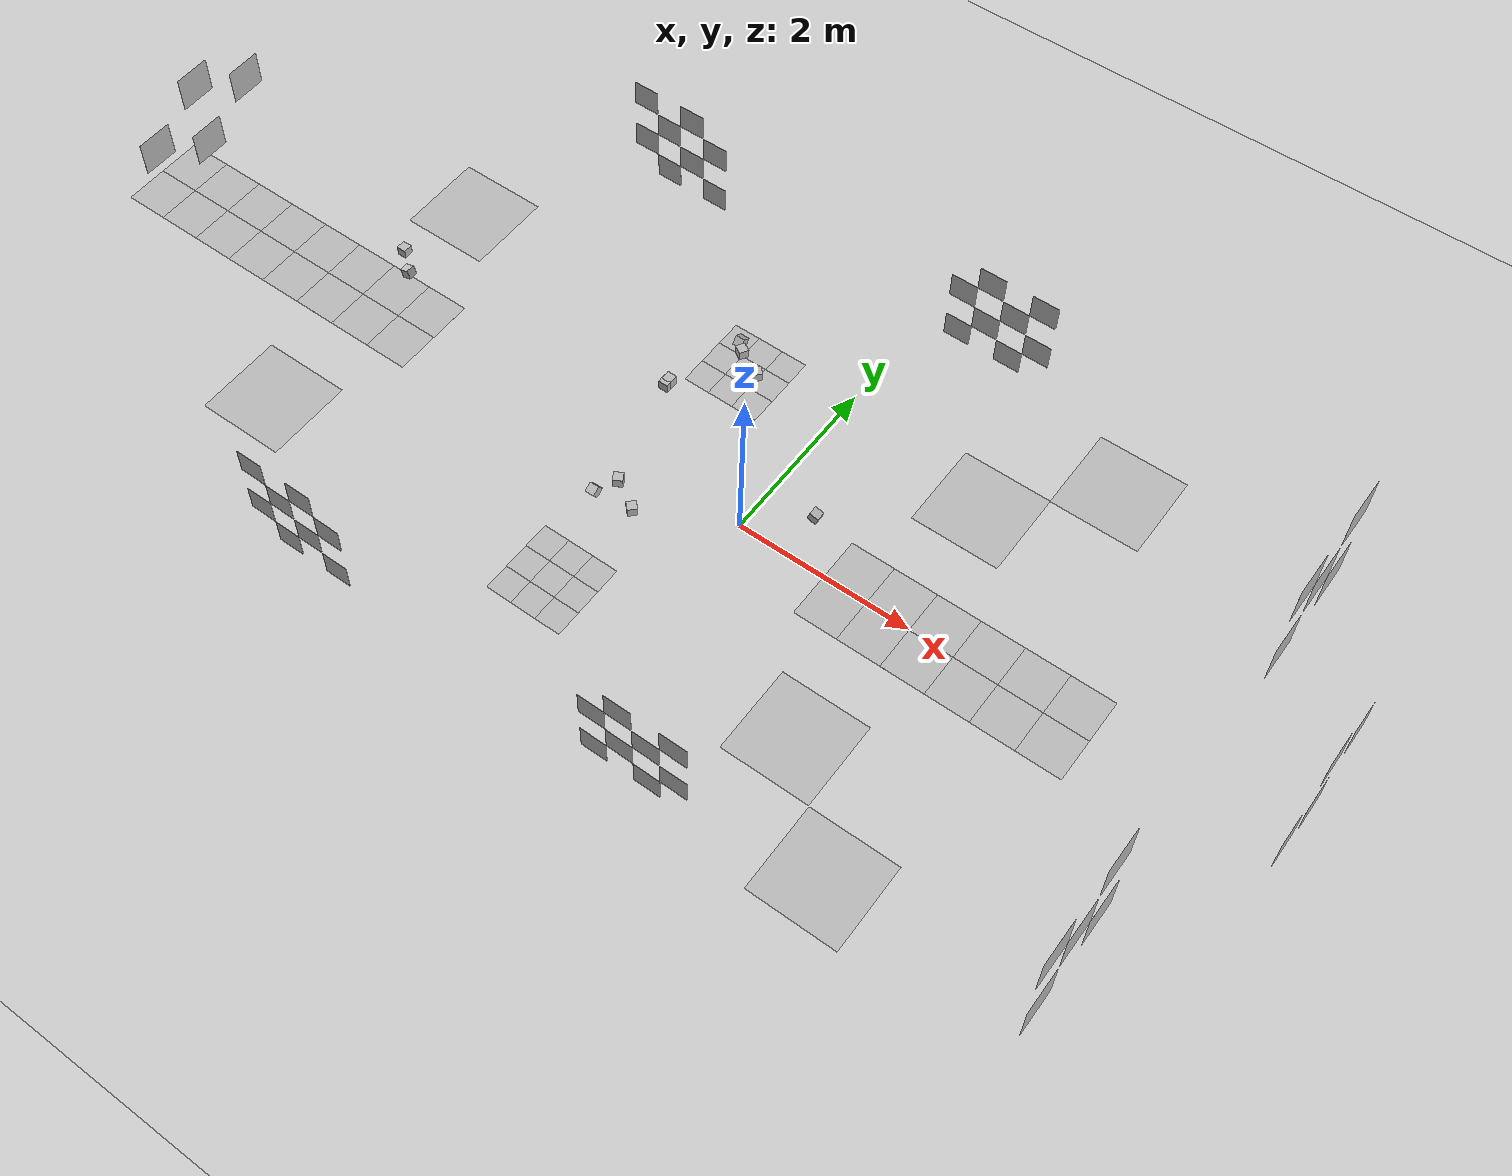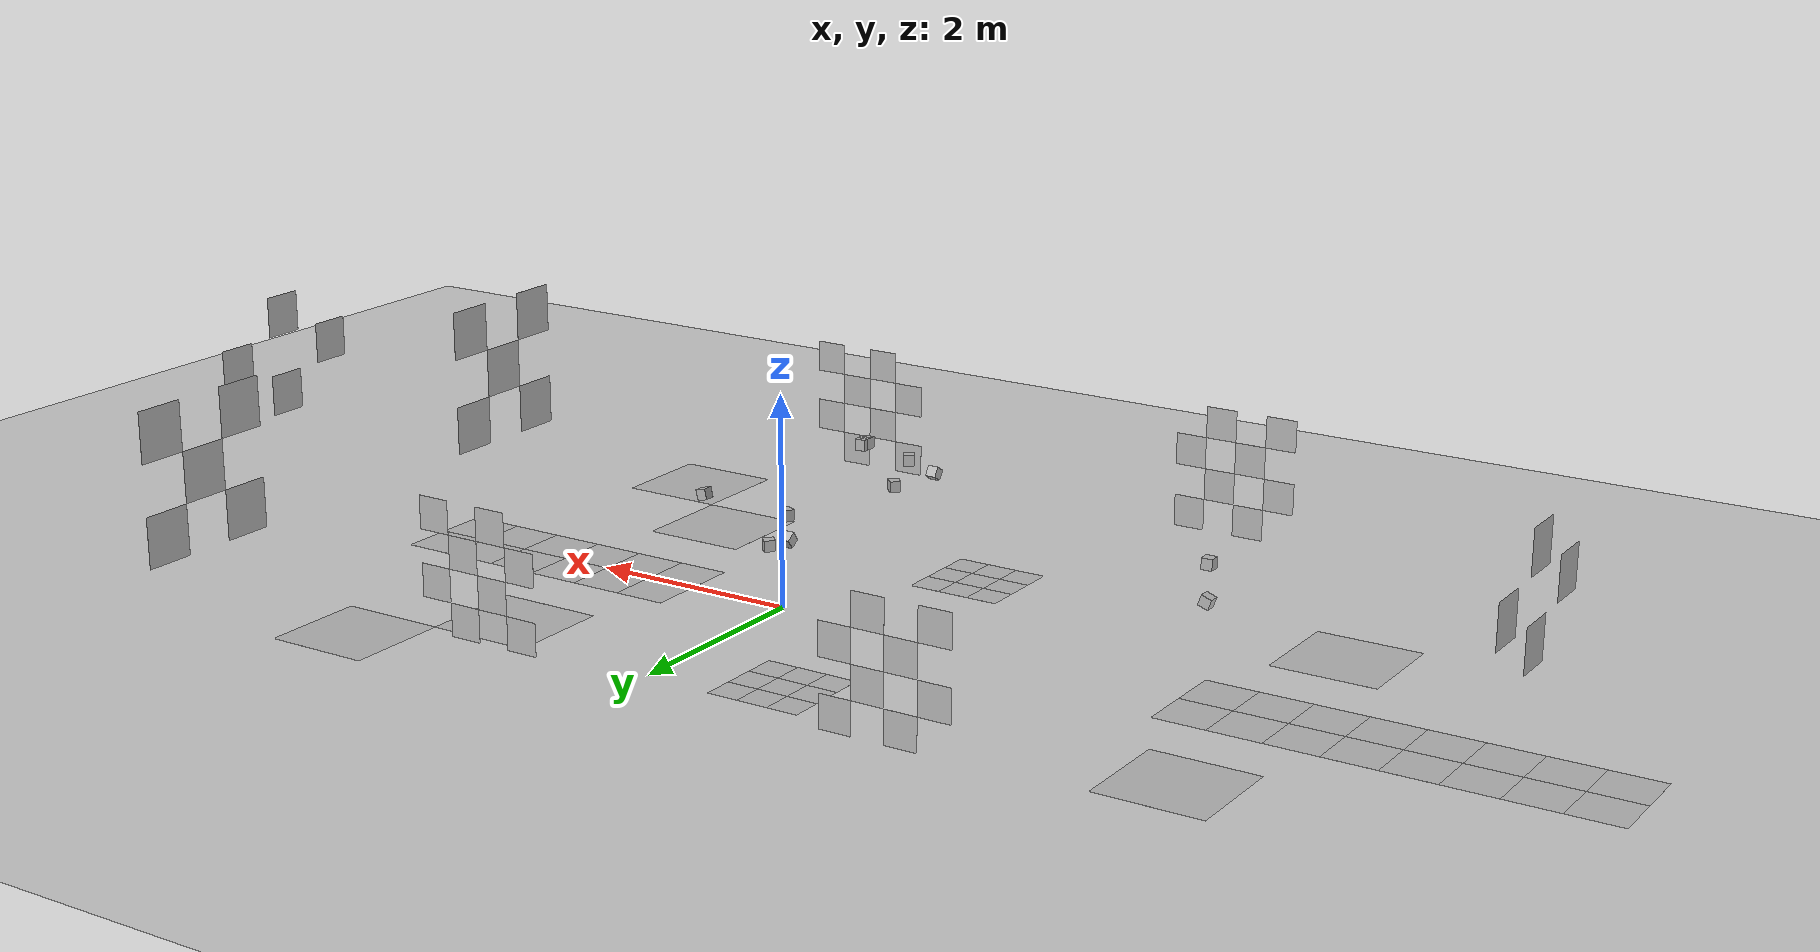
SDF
<sdf version="1.7">
 <world name="default">
  <light name="sun" type="directional">
   <pose>0 0 10 0 -0 0</pose>
   <diffuse>0.8 0.8 0.8 1</diffuse>
   <specular>0.2 0.2 0.2 1</specular>
   <attenuation>
    <range>1000</range>
    <constant>0.9</constant>
    <linear>0.01</linear>
    <quadratic>0.001</quadratic>
   </attenuation>
   <direction>-0.5 0.1 -0.9</direction>
   <spot><inner_angle>0</inner_angle><outer_angle>0</outer_angle><falloff>0</falloff></spot>
  </light>
  <model name="ground_plane">
   <pose>1.6 0 -0.001 0 -0 0</pose>
   <static>1</static>
   <link name="link">
    <collision name="collision">
     <geometry><plane><normal>0 0 1</normal><size>100 100</size></plane></geometry>
     <surface>
      <contact><collide_bitmask>65535</collide_bitmask></contact>
      <friction><ode><mu>100</mu><mu2>50</mu2></ode></friction>
     </surface>
    </collision>
    <visual name="visual">
     <cast_shadows>0</cast_shadows>
     <geometry><plane><normal>0 0 1</normal><size>100 100</size></plane></geometry>
     <material>
      <script><uri>file://media/materials/scripts/gazebo.material</uri><name>Gazebo/Grey</name></script>
     </material>
    </visual>
   </link>
  </model>
  <gravity>0 0 -9.8</gravity>
  <magnetic_field>6e-06 2.3e-05 -4.2e-05</magnetic_field>
  <atmosphere type="adiabatic"/>
  <physics type="ode">
   <max_step_size>0.001</max_step_size>
   <real_time_factor>1</real_time_factor>
   <real_time_update_rate>1000</real_time_update_rate>
  </physics>
  <scene><ambient>0.4 0.4 0.4 1</ambient><background>0.7 0.7 0.7 1</background><shadows>1</shadows></scene>
  <spherical_coordinates>
   <surface_model>EARTH_WGS84</surface_model>
   <latitude_deg>0</latitude_deg>
   <longitude_deg>0</longitude_deg>
   <elevation>0</elevation>
   <heading_deg>0</heading_deg>
  </spherical_coordinates>
  <model name="Apriltag36_11_00000">
   <link name="main">
    <visual name="main_Visual">
     <geometry><box><size>0.5 0.5 0.0001</size></box></geometry>
     <material>
      <script>
       <uri>model://Apriltag36_11_00000/materials/scripts</uri>
       <uri>model://Apriltag36_11_00000/materials/textures</uri>
       <name>Apriltag36_11_00000</name>
      </script>
     </material>
    </visual>
    <collision name="collision"><geometry><box><size>0.5 0.5 0.0001</size></box></geometry></collision>
   </link>
   <static>1</static>
   <pose>3.75 0.25 0 0 -0 0</pose>
  </model>
  <model name="Apriltag36_11_00001">
   <link name="main">
    <visual name="main_Visual">
     <geometry><box><size>0.5 0.5 0.0001</size></box></geometry>
     <material>
      <script>
       <uri>model://Apriltag36_11_00001/materials/scripts</uri>
       <uri>model://Apriltag36_11_00001/materials/textures</uri>
       <name>Apriltag36_11_00001</name>
      </script>
     </material>
    </visual>
    <collision name="collision"><geometry><box><size>0.5 0.5 0.0001</size></box></geometry></collision>
   </link>
   <static>1</static>
   <pose>3.25 0.25 0 0 -0 0</pose>
  </model>
  <model name="Apriltag36_11_00002">
   <link name="main">
    <visual name="main_Visual">
     <geometry><box><size>0.5 0.5 0.0001</size></box></geometry>
     <material>
      <script>
       <uri>model://Apriltag36_11_00002/materials/scripts</uri>
       <uri>model://Apriltag36_11_00002/materials/textures</uri>
       <name>Apriltag36_11_00002</name>
      </script>
     </material>
    </visual>
    <collision name="collision"><geometry><box><size>0.5 0.5 0.0001</size></box></geometry></collision>
   </link>
   <static>1</static>
   <pose>2.75 0.25 0 0 -0 0</pose>
  </model>
  <model name="Apriltag36_11_00003">
   <link name="main">
    <visual name="main_Visual">
     <geometry><box><size>0.5 0.5 0.0001</size></box></geometry>
     <material>
      <script>
       <uri>model://Apriltag36_11_00003/materials/scripts</uri>
       <uri>model://Apriltag36_11_00003/materials/textures</uri>
       <name>Apriltag36_11_00003</name>
      </script>
     </material>
    </visual>
    <collision name="collision"><geometry><box><size>0.5 0.5 0.0001</size></box></geometry></collision>
   </link>
   <static>1</static>
   <pose>2.25 0.25 0 0 -0 0</pose>
  </model>
  <model name="Apriltag36_11_00004">
   <link name="main">
    <visual name="main_Visual">
     <geometry><box><size>0.5 0.5 0.0001</size></box></geometry>
     <material>
      <script>
       <uri>model://Apriltag36_11_00004/materials/scripts</uri>
       <uri>model://Apriltag36_11_00004/materials/textures</uri>
       <name>Apriltag36_11_00004</name>
      </script>
     </material>
    </visual>
    <collision name="collision"><geometry><box><size>0.5 0.5 0.0001</size></box></geometry></collision>
   </link>
   <static>1</static>
   <pose>3.75 -0.25 0 0 -0 0</pose>
  </model>
  <model name="Apriltag36_11_00005">
   <link name="main">
    <visual name="main_Visual">
     <geometry><box><size>0.5 0.5 0.0001</size></box></geometry>
     <material>
      <script>
       <uri>model://Apriltag36_11_00005/materials/scripts</uri>
       <uri>model://Apriltag36_11_00005/materials/textures</uri>
       <name>Apriltag36_11_00005</name>
      </script>
     </material>
    </visual>
    <collision name="collision"><geometry><box><size>0.5 0.5 0.0001</size></box></geometry></collision>
   </link>
   <static>1</static>
   <pose>3.25 -0.25 0 0 -0 0</pose>
  </model>
  <model name="Apriltag36_11_00006">
   <link name="main">
    <visual name="main_Visual">
     <geometry><box><size>0.5 0.5 0.0001</size></box></geometry>
     <material>
      <script>
       <uri>model://Apriltag36_11_00006/materials/scripts</uri>
       <uri>model://Apriltag36_11_00006/materials/textures</uri>
       <name>Apriltag36_11_00006</name>
      </script>
     </material>
    </visual>
    <collision name="collision"><geometry><box><size>0.5 0.5 0.0001</size></box></geometry></collision>
   </link>
   <static>1</static>
   <pose>2.75 -0.25 0 0 -0 0</pose>
  </model>
  <model name="Apriltag36_11_00007">
   <link name="main">
    <visual name="main_Visual">
     <geometry><box><size>0.5 0.5 0.0001</size></box></geometry>
     <material>
      <script>
       <uri>model://Apriltag36_11_00007/materials/scripts</uri>
       <uri>model://Apriltag36_11_00007/materials/textures</uri>
       <name>Apriltag36_11_00007</name>
      </script>
     </material>
    </visual>
    <collision name="collision"><geometry><box><size>0.5 0.5 0.0001</size></box></geometry></collision>
   </link>
   <static>1</static>
   <pose>2.25 -0.25 0 0 -0 0</pose>
  </model>
  <model name="Apriltag36_11_00008">
   <link name="main">
    <visual name="main_Visual">
     <geometry><box><size>0.5 0.5 0.0001</size></box></geometry>
     <material>
      <script>
       <uri>model://Apriltag36_11_00008/materials/scripts</uri>
       <uri>model://Apriltag36_11_00008/materials/textures</uri>
       <name>Apriltag36_11_00008</name>
      </script>
     </material>
    </visual>
    <collision name="collision"><geometry><box><size>0.5 0.5 0.0001</size></box></geometry></collision>
   </link>
   <static>1</static>
   <pose>-5.25 0.25 0 0 -0 0</pose>
  </model>
  <model name="Apriltag36_11_00009">
   <link name="main">
    <visual name="main_Visual">
     <geometry><box><size>0.5 0.5 0.0001</size></box></geometry>
     <material>
      <script>
       <uri>model://Apriltag36_11_00009/materials/scripts</uri>
       <uri>model://Apriltag36_11_00009/materials/textures</uri>
       <name>Apriltag36_11_00009</name>
      </script>
     </material>
    </visual>
    <collision name="collision"><geometry><box><size>0.5 0.5 0.0001</size></box></geometry></collision>
   </link>
   <static>1</static>
   <pose>-5.75 0.25 0 0 -0 0</pose>
  </model>
  <model name="Apriltag36_11_00010">
   <link name="main">
    <visual name="main_Visual">
     <geometry><box><size>0.5 0.5 0.0001</size></box></geometry>
     <material>
      <script>
       <uri>model://Apriltag36_11_00010/materials/scripts</uri>
       <uri>model://Apriltag36_11_00010/materials/textures</uri>
       <name>Apriltag36_11_00010</name>
      </script>
     </material>
    </visual>
    <collision name="collision"><geometry><box><size>0.5 0.5 0.0001</size></box></geometry></collision>
   </link>
   <static>1</static>
   <pose>-6.25 0.25 0 0 -0 0</pose>
  </model>
  <model name="Apriltag36_11_00011">
   <link name="main">
    <visual name="main_Visual">
     <geometry><box><size>0.5 0.5 0.0001</size></box></geometry>
     <material>
      <script>
       <uri>model://Apriltag36_11_00011/materials/scripts</uri>
       <uri>model://Apriltag36_11_00011/materials/textures</uri>
       <name>Apriltag36_11_00011</name>
      </script>
     </material>
    </visual>
    <collision name="collision"><geometry><box><size>0.5 0.5 0.0001</size></box></geometry></collision>
   </link>
   <static>1</static>
   <pose>-6.75 0.25 0 0 -0 0</pose>
  </model>
  <model name="Apriltag36_11_00012">
   <link name="main">
    <visual name="main_Visual">
     <geometry><box><size>0.5 0.5 0.0001</size></box></geometry>
     <material>
      <script>
       <uri>model://Apriltag36_11_00012/materials/scripts</uri>
       <uri>model://Apriltag36_11_00012/materials/textures</uri>
       <name>Apriltag36_11_00012</name>
      </script>
     </material>
    </visual>
    <collision name="collision"><geometry><box><size>0.5 0.5 0.0001</size></box></geometry></collision>
   </link>
   <static>1</static>
   <pose>-5.25 -0.25 0 0 -0 0</pose>
  </model>
  <model name="Apriltag36_11_00013">
   <link name="main">
    <visual name="main_Visual">
     <geometry><box><size>0.5 0.5 0.0001</size></box></geometry>
     <material>
      <script>
       <uri>model://Apriltag36_11_00013/materials/scripts</uri>
       <uri>model://Apriltag36_11_00013/materials/textures</uri>
       <name>Apriltag36_11_00013</name>
      </script>
     </material>
    </visual>
    <collision name="collision"><geometry><box><size>0.5 0.5 0.0001</size></box></geometry></collision>
   </link>
   <static>1</static>
   <pose>-5.75 -0.25 0 0 -0 0</pose>
  </model>
  <model name="Apriltag36_11_00014">
   <link name="main">
    <visual name="main_Visual">
     <geometry><box><size>0.5 0.5 0.0001</size></box></geometry>
     <material>
      <script>
       <uri>model://Apriltag36_11_00014/materials/scripts</uri>
       <uri>model://Apriltag36_11_00014/materials/textures</uri>
       <name>Apriltag36_11_00014</name>
      </script>
     </material>
    </visual>
    <collision name="collision"><geometry><box><size>0.5 0.5 0.0001</size></box></geometry></collision>
   </link>
   <static>1</static>
   <pose>-6.25 -0.25 0 0 -0 0</pose>
  </model>
  <model name="Apriltag36_11_00015">
   <link name="main">
    <visual name="main_Visual">
     <geometry><box><size>0.5 0.5 0.0001</size></box></geometry>
     <material>
      <script>
       <uri>model://Apriltag36_11_00015/materials/scripts</uri>
       <uri>model://Apriltag36_11_00015/materials/textures</uri>
       <name>Apriltag36_11_00015</name>
      </script>
     </material>
    </visual>
    <collision name="collision"><geometry><box><size>0.5 0.5 0.0001</size></box></geometry></collision>
   </link>
   <static>1</static>
   <pose>-6.75 -0.25 0 0 -0 0</pose>
  </model>
  <model name="Apriltag36_11_00016">
   <link name="main">
    <pose>0 0 0 0 -1.5707 0</pose>
    <visual name="main_Visual">
     <geometry><box><size>0.4 0.4 0.0001</size></box></geometry>
     <material>
      <script>
       <uri>model://Apriltag36_11_00016/materials/scripts</uri>
       <uri>model://Apriltag36_11_00016/materials/textures</uri>
       <name>Apriltag36_11_00016</name>
      </script>
     </material>
    </visual>
    <collision name="collision"><geometry><box><size>0.4 0.4 0.0001</size></box></geometry></collision>
   </link>
   <static>1</static>
   <pose>6 0 1.9 0 -0 0</pose>
  </model>
  <model name="Apriltag36_11_00017">
   <link name="main">
    <pose>0 0 0 0 -1.5707 0</pose>
    <visual name="main_Visual">
     <geometry><box><size>0.4 0.4 0.0001</size></box></geometry>
     <material>
      <script>
       <uri>model://Apriltag36_11_00017/materials/scripts</uri>
       <uri>model://Apriltag36_11_00017/materials/textures</uri>
       <name>Apriltag36_11_00017</name>
      </script>
     </material>
    </visual>
    <collision name="collision"><geometry><box><size>0.4 0.4 0.0001</size></box></geometry></collision>
   </link>
   <static>1</static>
   <pose>6 0.65 1.5 0 -0 0</pose>
  </model>
  <model name="Apriltag36_11_00018">
   <link name="main">
    <pose>0 0 0 0 -1.5707 0</pose>
    <visual name="main_Visual">
     <geometry><box><size>0.4 0.4 0.0001</size></box></geometry>
     <material>
      <script>
       <uri>model://Apriltag36_11_00018/materials/scripts</uri>
       <uri>model://Apriltag36_11_00018/materials/textures</uri>
       <name>Apriltag36_11_00018</name>
      </script>
     </material>
    </visual>
    <collision name="collision"><geometry><box><size>0.4 0.4 0.0001</size></box></geometry></collision>
   </link>
   <static>1</static>
   <pose>6 -0.65 1.5 0 -0 0</pose>
  </model>
  <model name="Apriltag36_11_00019">
   <link name="main">
    <pose>0 0 0 0 -1.5707 0</pose>
    <visual name="main_Visual">
     <geometry><box><size>0.4 0.4 0.0001</size></box></geometry>
     <material>
      <script>
       <uri>model://Apriltag36_11_00019/materials/scripts</uri>
       <uri>model://Apriltag36_11_00019/materials/textures</uri>
       <name>Apriltag36_11_00019</name>
      </script>
     </material>
    </visual>
    <collision name="collision"><geometry><box><size>0.4 0.4 0.0001</size></box></geometry></collision>
   </link>
   <static>1</static>
   <pose>6 0 1.1 0 -0 0</pose>
  </model>
  <model name="Apriltag36_11_00020">
   <link name="main">
    <pose>0 0 0 3.14159 -1.5707 -0</pose>
    <visual name="main_Visual">
     <geometry><box><size>0.4 0.4 0.0001</size></box></geometry>
     <material>
      <script>
       <uri>model://Apriltag36_11_00020/materials/scripts</uri>
       <uri>model://Apriltag36_11_00020/materials/textures</uri>
       <name>Apriltag36_11_00020</name>
      </script>
     </material>
    </visual>
    <collision name="collision"><geometry><box><size>0.4 0.4 0.0001</size></box></geometry></collision>
   </link>
   <static>1</static>
   <pose>-7 0 1.9 0 -0 0</pose>
  </model>
  <model name="Apriltag36_11_00021">
   <link name="main">
    <pose>0 0 0 3.14159 -1.5707 -0</pose>
    <visual name="main_Visual">
     <geometry><box><size>0.4 0.4 0.0001</size></box></geometry>
     <material>
      <script>
       <uri>model://Apriltag36_11_00021/materials/scripts</uri>
       <uri>model://Apriltag36_11_00021/materials/textures</uri>
       <name>Apriltag36_11_00021</name>
      </script>
     </material>
    </visual>
    <collision name="collision"><geometry><box><size>0.4 0.4 0.0001</size></box></geometry></collision>
   </link>
   <static>1</static>
   <pose>-7 0.65 1.5 0 -0 0</pose>
  </model>
  <model name="Apriltag36_11_00022">
   <link name="main">
    <pose>0 0 0 3.14159 -1.5707 -0</pose>
    <visual name="main_Visual">
     <geometry><box><size>0.4 0.4 0.0001</size></box></geometry>
     <material>
      <script>
       <uri>model://Apriltag36_11_00022/materials/scripts</uri>
       <uri>model://Apriltag36_11_00022/materials/textures</uri>
       <name>Apriltag36_11_00022</name>
      </script>
     </material>
    </visual>
    <collision name="collision"><geometry><box><size>0.4 0.4 0.0001</size></box></geometry></collision>
   </link>
   <static>1</static>
   <pose>-7 -0.65 1.5 0 -0 0</pose>
  </model>
  <model name="Apriltag36_11_00023">
   <link name="main">
    <pose>0 0 0 3.14159 -1.5707 -0</pose>
    <visual name="main_Visual">
     <geometry><box><size>0.4 0.4 0.0001</size></box></geometry>
     <material>
      <script>
       <uri>model://Apriltag36_11_00023/materials/scripts</uri>
       <uri>model://Apriltag36_11_00023/materials/textures</uri>
       <name>Apriltag36_11_00023</name>
      </script>
     </material>
    </visual>
    <collision name="collision"><geometry><box><size>0.4 0.4 0.0001</size></box></geometry></collision>
   </link>
   <static>1</static>
   <pose>-7 0 1.1 0 -0 0</pose>
  </model>
  <model name="Apriltag36_11_00024">
   <link name="main">
    <pose>0 0 0 0 -1.5707 0</pose>
    <visual name="main_Visual">
     <geometry><box><size>0.5 0.5 0.0001</size></box></geometry>
     <material>
      <script>
       <uri>model://Apriltag36_11_00024/materials/scripts</uri>
       <uri>model://Apriltag36_11_00024/materials/textures</uri>
       <name>Apriltag36_11_00024</name>
      </script>
     </material>
    </visual>
    <collision name="collision"><geometry><box><size>0.5 0.5 0.0001</size></box></geometry></collision>
   </link>
   <static>1</static>
   <pose>5 1.65 1.5 0 -0 0</pose>
  </model>
  <model name="Apriltag36_11_00025">
   <link name="main">
    <pose>0 0 0 0 -1.5707 0</pose>
    <visual name="main_Visual">
     <geometry><box><size>0.5 0.5 0.0001</size></box></geometry>
     <material>
      <script>
       <uri>model://Apriltag36_11_00025/materials/scripts</uri>
       <uri>model://Apriltag36_11_00025/materials/textures</uri>
       <name>Apriltag36_11_00025</name>
      </script>
     </material>
    </visual>
    <collision name="collision"><geometry><box><size>0.5 0.5 0.0001</size></box></geometry></collision>
   </link>
   <static>1</static>
   <pose>5 1.65 0.5 0 -0 0</pose>
  </model>
  <model name="Apriltag36_11_00026">
   <link name="main">
    <pose>0 0 0 0 -1.5707 0</pose>
    <visual name="main_Visual">
     <geometry><box><size>0.5 0.5 0.0001</size></box></geometry>
     <material>
      <script>
       <uri>model://Apriltag36_11_00026/materials/scripts</uri>
       <uri>model://Apriltag36_11_00026/materials/textures</uri>
       <name>Apriltag36_11_00026</name>
      </script>
     </material>
    </visual>
    <collision name="collision"><geometry><box><size>0.5 0.5 0.0001</size></box></geometry></collision>
   </link>
   <static>1</static>
   <pose>5 -1.65 1.5 0 -0 0</pose>
  </model>
  <model name="Apriltag36_11_00027">
   <link name="main">
    <pose>0 0 0 0 -1.5707 0</pose>
    <visual name="main_Visual">
     <geometry><box><size>0.5 0.5 0.0001</size></box></geometry>
     <material>
      <script>
       <uri>model://Apriltag36_11_00027/materials/scripts</uri>
       <uri>model://Apriltag36_11_00027/materials/textures</uri>
       <name>Apriltag36_11_00027</name>
      </script>
     </material>
    </visual>
    <collision name="collision"><geometry><box><size>0.5 0.5 0.0001</size></box></geometry></collision>
   </link>
   <static>1</static>
   <pose>5 -1.65 0.5 0 -0 0</pose>
  </model>
  <model name="Apriltag36_11_00028">
   <link name="main">
    <pose>0 0 0 1.5707 -1.5707 0</pose>
    <visual name="main_Visual">
     <geometry><box><size>0.3 0.3 0.0001</size></box></geometry>
     <material>
      <script>
       <uri>model://Apriltag36_11_00028/materials/scripts</uri>
       <uri>model://Apriltag36_11_00028/materials/textures</uri>
       <name>Apriltag36_11_00028</name>
      </script>
     </material>
    </visual>
    <collision name="collision"><geometry><box><size>0.5 0.5 0.0001</size></box></geometry></collision>
   </link>
   <static>1</static>
   <pose>0.85 3 1.45 0 -0 0</pose>
  </model>
  <model name="Apriltag36_11_00029">
   <link name="main">
    <pose>0 0 0 1.5707 -1.5707 0</pose>
    <visual name="main_Visual">
     <geometry><box><size>0.3 0.3 0.0001</size></box></geometry>
     <material>
      <script>
       <uri>model://Apriltag36_11_00029/materials/scripts</uri>
       <uri>model://Apriltag36_11_00029/materials/textures</uri>
       <name>Apriltag36_11_00029</name>
      </script>
     </material>
    </visual>
    <collision name="collision"><geometry><box><size>0.5 0.5 0.0001</size></box></geometry></collision>
   </link>
   <static>1</static>
   <pose>1.45 3 1.45 0 -0 0</pose>
  </model>
  <model name="Apriltag36_11_00030">
   <link name="main">
    <pose>0 0 0 1.5707 -1.5707 0</pose>
    <visual name="main_Visual">
     <geometry><box><size>0.3 0.3 0.0001</size></box></geometry>
     <material>
      <script>
       <uri>model://Apriltag36_11_00030/materials/scripts</uri>
       <uri>model://Apriltag36_11_00030/materials/textures</uri>
       <name>Apriltag36_11_00030</name>
      </script>
     </material>
    </visual>
    <collision name="collision"><geometry><box><size>0.5 0.5 0.0001</size></box></geometry></collision>
   </link>
   <static>1</static>
   <pose>0.85 3 0.85 0 -0 0</pose>
  </model>
  <model name="Apriltag36_11_00031">
   <link name="main">
    <pose>0 0 0 1.5707 -1.5707 0</pose>
    <visual name="main_Visual">
     <geometry><box><size>0.3 0.3 0.0001</size></box></geometry>
     <material>
      <script>
       <uri>model://Apriltag36_11_00031/materials/scripts</uri>
       <uri>model://Apriltag36_11_00031/materials/textures</uri>
       <name>Apriltag36_11_00031</name>
      </script>
     </material>
    </visual>
    <collision name="collision"><geometry><box><size>0.5 0.5 0.0001</size></box></geometry></collision>
   </link>
   <static>1</static>
   <pose>1.15 3 1.15 0 -0 0</pose>
  </model>
  <model name="Apriltag36_11_00032">
   <link name="main">
    <pose>0 0 0 1.5707 -1.5707 0</pose>
    <visual name="main_Visual">
     <geometry><box><size>0.3 0.3 0.0001</size></box></geometry>
     <material>
      <script>
       <uri>model://Apriltag36_11_00032/materials/scripts</uri>
       <uri>model://Apriltag36_11_00032/materials/textures</uri>
       <name>Apriltag36_11_00032</name>
      </script>
     </material>
    </visual>
    <collision name="collision"><geometry><box><size>0.5 0.5 0.0001</size></box></geometry></collision>
   </link>
   <static>1</static>
   <pose>0.55 3 1.15 0 -0 0</pose>
  </model>
  <model name="Apriltag36_11_00033">
   <link name="main">
    <pose>0 0 0 1.5707 -1.5707 0</pose>
    <visual name="main_Visual">
     <geometry><box><size>0.3 0.3 0.0001</size></box></geometry>
     <material>
      <script>
       <uri>model://Apriltag36_11_00033/materials/scripts</uri>
       <uri>model://Apriltag36_11_00033/materials/textures</uri>
       <name>Apriltag36_11_00033</name>
      </script>
     </material>
    </visual>
    <collision name="collision"><geometry><box><size>0.5 0.5 0.0001</size></box></geometry></collision>
   </link>
   <static>1</static>
   <pose>1.45 3 0.85 0 -0 0</pose>
  </model>
  <model name="Apriltag36_11_00034">
   <link name="main">
    <pose>0 0 0 1.5707 -1.5707 0</pose>
    <visual name="main_Visual">
     <geometry><box><size>0.3 0.3 0.0001</size></box></geometry>
     <material>
      <script>
       <uri>model://Apriltag36_11_00034/materials/scripts</uri>
       <uri>model://Apriltag36_11_00034/materials/textures</uri>
       <name>Apriltag36_11_00034</name>
      </script>
     </material>
    </visual>
    <collision name="collision"><geometry><box><size>0.5 0.5 0.0001</size></box></geometry></collision>
   </link>
   <static>1</static>
   <pose>-2.85 3 1.45 0 -0 0</pose>
  </model>
  <model name="Apriltag36_11_00035">
   <link name="main">
    <pose>0 0 0 1.5707 -1.5707 0</pose>
    <visual name="main_Visual">
     <geometry><box><size>0.3 0.3 0.0001</size></box></geometry>
     <material>
      <script>
       <uri>model://Apriltag36_11_00035/materials/scripts</uri>
       <uri>model://Apriltag36_11_00035/materials/textures</uri>
       <name>Apriltag36_11_00035</name>
      </script>
     </material>
    </visual>
    <collision name="collision"><geometry><box><size>0.5 0.5 0.0001</size></box></geometry></collision>
   </link>
   <static>1</static>
   <pose>-2.55 3 1.15 0 -0 0</pose>
  </model>
  <model name="Apriltag36_11_00036">
   <link name="main">
    <pose>0 0 0 1.5707 -1.5707 0</pose>
    <visual name="main_Visual">
     <geometry><box><size>0.3 0.3 0.0001</size></box></geometry>
     <material>
      <script>
       <uri>model://Apriltag36_11_00036/materials/scripts</uri>
       <uri>model://Apriltag36_11_00036/materials/textures</uri>
       <name>Apriltag36_11_00036</name>
      </script>
     </material>
    </visual>
    <collision name="collision"><geometry><box><size>0.5 0.5 0.0001</size></box></geometry></collision>
   </link>
   <static>1</static>
   <pose>-3.15 3 1.15 0 -0 0</pose>
  </model>
  <model name="Apriltag36_11_00037">
   <link name="main">
    <pose>0 0 0 1.5707 -1.5707 0</pose>
    <visual name="main_Visual">
     <geometry><box><size>0.3 0.3 0.0001</size></box></geometry>
     <material>
      <script>
       <uri>model://Apriltag36_11_00037/materials/scripts</uri>
       <uri>model://Apriltag36_11_00037/materials/textures</uri>
       <name>Apriltag36_11_00037</name>
      </script>
     </material>
    </visual>
    <collision name="collision"><geometry><box><size>0.5 0.5 0.0001</size></box></geometry></collision>
   </link>
   <static>1</static>
   <pose>-2.55 3 0.55 0 -0 0</pose>
  </model>
  <model name="Apriltag36_11_00038">
   <link name="main">
    <pose>0 0 0 1.5707 -1.5707 0</pose>
    <visual name="main_Visual">
     <geometry><box><size>0.3 0.3 0.0001</size></box></geometry>
     <material>
      <script>
       <uri>model://Apriltag36_11_00038/materials/scripts</uri>
       <uri>model://Apriltag36_11_00038/materials/textures</uri>
       <name>Apriltag36_11_00038</name>
      </script>
     </material>
    </visual>
    <collision name="collision"><geometry><box><size>0.5 0.5 0.0001</size></box></geometry></collision>
   </link>
   <static>1</static>
   <pose>-2.85 3 0.85 0 -0 0</pose>
  </model>
  <model name="Apriltag36_11_00039">
   <link name="main">
    <pose>0 0 0 1.5707 -1.5707 0</pose>
    <visual name="main_Visual">
     <geometry><box><size>0.3 0.3 0.0001</size></box></geometry>
     <material>
      <script>
       <uri>model://Apriltag36_11_00039/materials/scripts</uri>
       <uri>model://Apriltag36_11_00039/materials/textures</uri>
       <name>Apriltag36_11_00039</name>
      </script>
     </material>
    </visual>
    <collision name="collision"><geometry><box><size>0.5 0.5 0.0001</size></box></geometry></collision>
   </link>
   <static>1</static>
   <pose>-3.15 3 0.55 0 -0 0</pose>
  </model>
  <model name="Apriltag36_11_00040">
   <link name="main">
    <pose>0 0 0 -1.5707 -1.5707 -0</pose>
    <visual name="main_Visual">
     <geometry><box><size>0.3 0.3 0.0001</size></box></geometry>
     <material>
      <script>
       <uri>model://Apriltag36_11_00040/materials/scripts</uri>
       <uri>model://Apriltag36_11_00040/materials/textures</uri>
       <name>Apriltag36_11_00040</name>
      </script>
     </material>
    </visual>
    <collision name="collision"><geometry><box><size>0.5 0.5 0.0001</size></box></geometry></collision>
   </link>
   <static>1</static>
   <pose>1.15 -3 1.15 0 -0 0</pose>
  </model>
  <model name="Apriltag36_11_00041">
   <link name="main">
    <pose>0 0 0 -1.5707 -1.5707 -0</pose>
    <visual name="main_Visual">
     <geometry><box><size>0.3 0.3 0.0001</size></box></geometry>
     <material>
      <script>
       <uri>model://Apriltag36_11_00041/materials/scripts</uri>
       <uri>model://Apriltag36_11_00041/materials/textures</uri>
       <name>Apriltag36_11_00041</name>
      </script>
     </material>
    </visual>
    <collision name="collision"><geometry><box><size>0.5 0.5 0.0001</size></box></geometry></collision>
   </link>
   <static>1</static>
   <pose>0.85 -3 0.85 0 -0 0</pose>
  </model>
  <model name="Apriltag36_11_00042">
   <link name="main">
    <pose>0 0 0 -1.5707 -1.5707 -0</pose>
    <visual name="main_Visual">
     <geometry><box><size>0.3 0.3 0.0001</size></box></geometry>
     <material>
      <script>
       <uri>model://Apriltag36_11_00042/materials/scripts</uri>
       <uri>model://Apriltag36_11_00042/materials/textures</uri>
       <name>Apriltag36_11_00042</name>
      </script>
     </material>
    </visual>
    <collision name="collision"><geometry><box><size>0.5 0.5 0.0001</size></box></geometry></collision>
   </link>
   <static>1</static>
   <pose>0.85 -3 1.45 0 -0 0</pose>
  </model>
  <model name="Apriltag36_11_00043">
   <link name="main">
    <pose>0 0 0 -1.5707 -1.5707 -0</pose>
    <visual name="main_Visual">
     <geometry><box><size>0.3 0.3 0.0001</size></box></geometry>
     <material>
      <script>
       <uri>model://Apriltag36_11_00043/materials/scripts</uri>
       <uri>model://Apriltag36_11_00043/materials/textures</uri>
       <name>Apriltag36_11_00043</name>
      </script>
     </material>
    </visual>
    <collision name="collision"><geometry><box><size>0.5 0.5 0.0001</size></box></geometry></collision>
   </link>
   <static>1</static>
   <pose>0.55 -3 1.15 0 -0 0</pose>
  </model>
  <model name="Apriltag36_11_00044">
   <link name="main">
    <pose>0 0 0 -1.5707 -1.5707 -0</pose>
    <visual name="main_Visual">
     <geometry><box><size>0.3 0.3 0.0001</size></box></geometry>
     <material>
      <script>
       <uri>model://Apriltag36_11_00044/materials/scripts</uri>
       <uri>model://Apriltag36_11_00044/materials/textures</uri>
       <name>Apriltag36_11_00044</name>
      </script>
     </material>
    </visual>
    <collision name="collision"><geometry><box><size>0.5 0.5 0.0001</size></box></geometry></collision>
   </link>
   <static>1</static>
   <pose>1.15 -3 0.55 0 -0 0</pose>
  </model>
  <model name="Apriltag36_11_00045">
   <link name="main">
    <pose>0 0 0 -1.5707 -1.5707 -0</pose>
    <visual name="main_Visual">
     <geometry><box><size>0.3 0.3 0.0001</size></box></geometry>
     <material>
      <script>
       <uri>model://Apriltag36_11_00045/materials/scripts</uri>
       <uri>model://Apriltag36_11_00045/materials/textures</uri>
       <name>Apriltag36_11_00045</name>
      </script>
     </material>
    </visual>
    <collision name="collision"><geometry><box><size>0.5 0.5 0.0001</size></box></geometry></collision>
   </link>
   <static>1</static>
   <pose>0.55 -3 0.55 0 -0 0</pose>
  </model>
  <model name="Apriltag36_11_00046">
   <link name="main">
    <pose>0 0 0 -1.5707 -1.5707 -0</pose>
    <visual name="main_Visual">
     <geometry><box><size>0.3 0.3 0.0001</size></box></geometry>
     <material>
      <script>
       <uri>model://Apriltag36_11_00046/materials/scripts</uri>
       <uri>model://Apriltag36_11_00046/materials/textures</uri>
       <name>Apriltag36_11_00046</name>
      </script>
     </material>
    </visual>
    <collision name="collision"><geometry><box><size>0.5 0.5 0.0001</size></box></geometry></collision>
   </link>
   <static>1</static>
   <pose>-2.85 -3 1.45 0 -0 0</pose>
  </model>
  <model name="Apriltag36_11_00047">
   <link name="main">
    <pose>0 0 0 -1.5707 -1.5707 -0</pose>
    <visual name="main_Visual">
     <geometry><box><size>0.3 0.3 0.0001</size></box></geometry>
     <material>
      <script>
       <uri>model://Apriltag36_11_00047/materials/scripts</uri>
       <uri>model://Apriltag36_11_00047/materials/textures</uri>
       <name>Apriltag36_11_00047</name>
      </script>
     </material>
    </visual>
    <collision name="collision"><geometry><box><size>0.5 0.5 0.0001</size></box></geometry></collision>
   </link>
   <static>1</static>
   <pose>-3.15 -3 1.15 0 -0 0</pose>
  </model>
  <model name="Apriltag36_11_00048">
   <link name="main">
    <pose>0 0 0 -1.5707 -1.5707 -0</pose>
    <visual name="main_Visual">
     <geometry><box><size>0.3 0.3 0.0001</size></box></geometry>
     <material>
      <script>
       <uri>model://Apriltag36_11_00048/materials/scripts</uri>
       <uri>model://Apriltag36_11_00048/materials/textures</uri>
       <name>Apriltag36_11_00048</name>
      </script>
     </material>
    </visual>
    <collision name="collision"><geometry><box><size>0.5 0.5 0.0001</size></box></geometry></collision>
   </link>
   <static>1</static>
   <pose>-3.15 -3 0.55 0 -0 0</pose>
  </model>
  <model name="Apriltag36_11_00049">
   <link name="main">
    <pose>0 0 0 -1.5707 -1.5707 -0</pose>
    <visual name="main_Visual">
     <geometry><box><size>0.3 0.3 0.0001</size></box></geometry>
     <material>
      <script>
       <uri>model://Apriltag36_11_00049/materials/scripts</uri>
       <uri>model://Apriltag36_11_00049/materials/textures</uri>
       <name>Apriltag36_11_00049</name>
      </script>
     </material>
    </visual>
    <collision name="collision"><geometry><box><size>0.5 0.5 0.0001</size></box></geometry></collision>
   </link>
   <static>1</static>
   <pose>-3.45 -3 1.45 0 -0 0</pose>
  </model>
  <model name="Apriltag36_11_00050">
   <link name="main">
    <pose>0 0 0 -1.5707 -1.5707 -0</pose>
    <visual name="main_Visual">
     <geometry><box><size>0.3 0.3 0.0001</size></box></geometry>
     <material>
      <script>
       <uri>model://Apriltag36_11_00050/materials/scripts</uri>
       <uri>model://Apriltag36_11_00050/materials/textures</uri>
       <name>Apriltag36_11_00050</name>
      </script>
     </material>
    </visual>
    <collision name="collision"><geometry><box><size>0.5 0.5 0.0001</size></box></geometry></collision>
   </link>
   <static>1</static>
   <pose>-2.85 -3 0.85 0 -0 0</pose>
  </model>
  <model name="Apriltag36_11_00051">
   <link name="main">
    <pose>0 0 0 -1.5707 -1.5707 -0</pose>
    <visual name="main_Visual">
     <geometry><box><size>0.3 0.3 0.0001</size></box></geometry>
     <material>
      <script>
       <uri>model://Apriltag36_11_00051/materials/scripts</uri>
       <uri>model://Apriltag36_11_00051/materials/textures</uri>
       <name>Apriltag36_11_00051</name>
      </script>
     </material>
    </visual>
    <collision name="collision"><geometry><box><size>0.5 0.5 0.0001</size></box></geometry></collision>
   </link>
   <static>1</static>
   <pose>-3.45 -3 0.85 0 -0 0</pose>
  </model>
  <model name="Apriltag36_11_00052">
   <link name="main">
    <visual name="main_Visual">
     <geometry><box><size>1 1 0.0001</size></box></geometry>
     <material>
      <script>
       <uri>model://Apriltag36_11_00052/materials/scripts</uri>
       <uri>model://Apriltag36_11_00052/materials/textures</uri>
       <name>Apriltag36_11_00052</name>
      </script>
     </material>
    </visual>
    <collision name="collision"><geometry><box><size>1 1 0.0001</size></box></geometry></collision>
   </link>
   <static>1</static>
   <pose>1.8 1.6 0 0 -0 0</pose>
  </model>
  <model name="Apriltag36_11_00053">
   <link name="main">
    <visual name="main_Visual">
     <geometry><box><size>1 1 0.0001</size></box></geometry>
     <material>
      <script>
       <uri>model://Apriltag36_11_00053/materials/scripts</uri>
       <uri>model://Apriltag36_11_00053/materials/textures</uri>
       <name>Apriltag36_11_00053</name>
      </script>
     </material>
    </visual>
    <collision name="collision"><geometry><box><size>1 1 0.0001</size></box></geometry></collision>
   </link>
   <static>1</static>
   <pose>1.8 -1.6 0 0 -0 0</pose>
  </model>
  <model name="Apriltag36_11_00054">
   <link name="main">
    <visual name="main_Visual">
     <geometry><box><size>1 1 0.0001</size></box></geometry>
     <material>
      <script>
       <uri>model://Apriltag36_11_00054/materials/scripts</uri>
       <uri>model://Apriltag36_11_00054/materials/textures</uri>
       <name>Apriltag36_11_00054</name>
      </script>
     </material>
    </visual>
    <collision name="collision"><geometry><box><size>1 1 0.0001</size></box></geometry></collision>
   </link>
   <static>1</static>
   <pose>-4.8 1.6 0 0 -0 0</pose>
  </model>
  <model name="Apriltag36_11_00055">
   <link name="main">
    <visual name="main_Visual">
     <geometry><box><size>1 1 0.0001</size></box></geometry>
     <material>
      <script>
       <uri>model://Apriltag36_11_00055/materials/scripts</uri>
       <uri>model://Apriltag36_11_00055/materials/textures</uri>
       <name>Apriltag36_11_00055</name>
      </script>
     </material>
    </visual>
    <collision name="collision"><geometry><box><size>1 1 0.0001</size></box></geometry></collision>
   </link>
   <static>1</static>
   <pose>-4.8 -1.6 0 0 -0 0</pose>
  </model>
  <model name="Apriltag36_11_00056">
   <link name="main">
    <visual name="main_Visual">
     <geometry><box><size>0.3 0.3 0.0001</size></box></geometry>
     <material>
      <script>
       <uri>model://Apriltag36_11_00056/materials/scripts</uri>
       <uri>model://Apriltag36_11_00056/materials/textures</uri>
       <name>Apriltag36_11_00056</name>
      </script>
     </material>
    </visual>
    <collision name="collision"><geometry><box><size>0.3 0.3 0.0001</size></box></geometry></collision>
   </link>
   <static>1</static>
   <pose>-0.8 1.9 0 0 -0 0</pose>
  </model>
  <model name="Apriltag36_11_00057">
   <link name="main">
    <visual name="main_Visual">
     <geometry><box><size>0.3 0.3 0.0001</size></box></geometry>
     <material>
      <script>
       <uri>model://Apriltag36_11_00057/materials/scripts</uri>
       <uri>model://Apriltag36_11_00057/materials/textures</uri>
       <name>Apriltag36_11_00057</name>
      </script>
     </material>
    </visual>
    <collision name="collision"><geometry><box><size>0.3 0.3 0.0001</size></box></geometry></collision>
   </link>
   <static>1</static>
   <pose>-0.8 1.6 0 0 -0 0</pose>
  </model>
  <model name="Apriltag36_11_00058">
   <link name="main">
    <visual name="main_Visual">
     <geometry><box><size>0.3 0.3 0.0001</size></box></geometry>
     <material>
      <script>
       <uri>model://Apriltag36_11_00058/materials/scripts</uri>
       <uri>model://Apriltag36_11_00058/materials/textures</uri>
       <name>Apriltag36_11_00058</name>
      </script>
     </material>
    </visual>
    <collision name="collision"><geometry><box><size>0.3 0.3 0.0001</size></box></geometry></collision>
   </link>
   <static>1</static>
   <pose>-0.8 1.3 0 0 -0 0</pose>
  </model>
  <model name="Apriltag36_11_00059">
   <link name="main">
    <visual name="main_Visual">
     <geometry><box><size>0.3 0.3 0.0001</size></box></geometry>
     <material>
      <script>
       <uri>model://Apriltag36_11_00059/materials/scripts</uri>
       <uri>model://Apriltag36_11_00059/materials/textures</uri>
       <name>Apriltag36_11_00059</name>
      </script>
     </material>
    </visual>
    <collision name="collision"><geometry><box><size>0.3 0.3 0.0001</size></box></geometry></collision>
   </link>
   <static>1</static>
   <pose>-1.1 1.9 0 0 -0 0</pose>
  </model>
  <model name="Apriltag36_11_00060">
   <link name="main">
    <visual name="main_Visual">
     <geometry><box><size>0.3 0.3 0.0001</size></box></geometry>
     <material>
      <script>
       <uri>model://Apriltag36_11_00060/materials/scripts</uri>
       <uri>model://Apriltag36_11_00060/materials/textures</uri>
       <name>Apriltag36_11_00060</name>
      </script>
     </material>
    </visual>
    <collision name="collision"><geometry><box><size>0.3 0.3 0.0001</size></box></geometry></collision>
   </link>
   <static>1</static>
   <pose>-1.1 1.6 0 0 -0 0</pose>
  </model>
  <model name="Apriltag36_11_00061">
   <link name="main">
    <visual name="main_Visual">
     <geometry><box><size>0.3 0.3 0.0001</size></box></geometry>
     <material>
      <script>
       <uri>model://Apriltag36_11_00061/materials/scripts</uri>
       <uri>model://Apriltag36_11_00061/materials/textures</uri>
       <name>Apriltag36_11_00061</name>
      </script>
     </material>
    </visual>
    <collision name="collision"><geometry><box><size>0.3 0.3 0.0001</size></box></geometry></collision>
   </link>
   <static>1</static>
   <pose>-1.1 1.3 0 0 -0 0</pose>
  </model>
  <model name="Apriltag36_11_00062">
   <link name="main">
    <visual name="main_Visual">
     <geometry><box><size>0.3 0.3 0.0001</size></box></geometry>
     <material>
      <script>
       <uri>model://Apriltag36_11_00062/materials/scripts</uri>
       <uri>model://Apriltag36_11_00062/materials/textures</uri>
       <name>Apriltag36_11_00062</name>
      </script>
     </material>
    </visual>
    <collision name="collision"><geometry><box><size>0.3 0.3 0.0001</size></box></geometry></collision>
   </link>
   <static>1</static>
   <pose>-1.4 1.9 0 0 -0 0</pose>
  </model>
  <model name="Apriltag36_11_00063">
   <link name="main">
    <visual name="main_Visual">
     <geometry><box><size>0.3 0.3 0.0001</size></box></geometry>
     <material>
      <script>
       <uri>model://Apriltag36_11_00063/materials/scripts</uri>
       <uri>model://Apriltag36_11_00063/materials/textures</uri>
       <name>Apriltag36_11_00063</name>
      </script>
     </material>
    </visual>
    <collision name="collision"><geometry><box><size>0.3 0.3 0.0001</size></box></geometry></collision>
   </link>
   <static>1</static>
   <pose>-1.4 1.6 0 0 -0 0</pose>
  </model>
  <model name="Apriltag36_11_00064">
   <link name="main">
    <visual name="main_Visual">
     <geometry><box><size>0.3 0.3 0.0001</size></box></geometry>
     <material>
      <script>
       <uri>model://Apriltag36_11_00064/materials/scripts</uri>
       <uri>model://Apriltag36_11_00064/materials/textures</uri>
       <name>Apriltag36_11_00064</name>
      </script>
     </material>
    </visual>
    <collision name="collision"><geometry><box><size>0.3 0.3 0.0001</size></box></geometry></collision>
   </link>
   <static>1</static>
   <pose>-1.4 1.3 0 0 -0 0</pose>
  </model>
  <model name="Apriltag36_11_00065">
   <link name="main">
    <visual name="main_Visual">
     <geometry><box><size>0.3 0.3 0.0001</size></box></geometry>
     <material>
      <script>
       <uri>model://Apriltag36_11_00065/materials/scripts</uri>
       <uri>model://Apriltag36_11_00065/materials/textures</uri>
       <name>Apriltag36_11_00065</name>
      </script>
     </material>
    </visual>
    <collision name="collision"><geometry><box><size>0.3 0.3 0.0001</size></box></geometry></collision>
   </link>
   <static>1</static>
   <pose>-0.8 -1.9 0 0 -0 0</pose>
  </model>
  <model name="Apriltag36_11_00066">
   <link name="main">
    <visual name="main_Visual">
     <geometry><box><size>0.3 0.3 0.0001</size></box></geometry>
     <material>
      <script>
       <uri>model://Apriltag36_11_00066/materials/scripts</uri>
       <uri>model://Apriltag36_11_00066/materials/textures</uri>
       <name>Apriltag36_11_00066</name>
      </script>
     </material>
    </visual>
    <collision name="collision"><geometry><box><size>0.3 0.3 0.0001</size></box></geometry></collision>
   </link>
   <static>1</static>
   <pose>-0.8 -1.6 0 0 -0 0</pose>
  </model>
  <model name="Apriltag36_11_00067">
   <link name="main">
    <visual name="main_Visual">
     <geometry><box><size>0.3 0.3 0.0001</size></box></geometry>
     <material>
      <script>
       <uri>model://Apriltag36_11_00067/materials/scripts</uri>
       <uri>model://Apriltag36_11_00067/materials/textures</uri>
       <name>Apriltag36_11_00067</name>
      </script>
     </material>
    </visual>
    <collision name="collision"><geometry><box><size>0.3 0.3 0.0001</size></box></geometry></collision>
   </link>
   <static>1</static>
   <pose>-0.8 -1.3 0 0 -0 0</pose>
  </model>
  <model name="Apriltag36_11_00068">
   <link name="main">
    <visual name="main_Visual">
     <geometry><box><size>0.3 0.3 0.0001</size></box></geometry>
     <material>
      <script>
       <uri>model://Apriltag36_11_00068/materials/scripts</uri>
       <uri>model://Apriltag36_11_00068/materials/textures</uri>
       <name>Apriltag36_11_00068</name>
      </script>
     </material>
    </visual>
    <collision name="collision"><geometry><box><size>0.3 0.3 0.0001</size></box></geometry></collision>
   </link>
   <static>1</static>
   <pose>-1.1 -1.9 0 0 -0 0</pose>
  </model>
  <model name="Apriltag36_11_00069">
   <link name="main">
    <visual name="main_Visual">
     <geometry><box><size>0.3 0.3 0.0001</size></box></geometry>
     <material>
      <script>
       <uri>model://Apriltag36_11_00069/materials/scripts</uri>
       <uri>model://Apriltag36_11_00069/materials/textures</uri>
       <name>Apriltag36_11_00069</name>
      </script>
     </material>
    </visual>
    <collision name="collision"><geometry><box><size>0.3 0.3 0.0001</size></box></geometry></collision>
   </link>
   <static>1</static>
   <pose>-1.1 -1.6 0 0 -0 0</pose>
  </model>
  <model name="Apriltag36_11_00070">
   <link name="main">
    <visual name="main_Visual">
     <geometry><box><size>0.3 0.3 0.0001</size></box></geometry>
     <material>
      <script>
       <uri>model://Apriltag36_11_00070/materials/scripts</uri>
       <uri>model://Apriltag36_11_00070/materials/textures</uri>
       <name>Apriltag36_11_00070</name>
      </script>
     </material>
    </visual>
    <collision name="collision"><geometry><box><size>0.3 0.3 0.0001</size></box></geometry></collision>
   </link>
   <static>1</static>
   <pose>-1.1 -1.3 0 0 -0 0</pose>
  </model>
  <model name="Apriltag36_11_00071">
   <link name="main">
    <visual name="main_Visual">
     <geometry><box><size>0.3 0.3 0.0001</size></box></geometry>
     <material>
      <script>
       <uri>model://Apriltag36_11_00071/materials/scripts</uri>
       <uri>model://Apriltag36_11_00071/materials/textures</uri>
       <name>Apriltag36_11_00071</name>
      </script>
     </material>
    </visual>
    <collision name="collision"><geometry><box><size>0.3 0.3 0.0001</size></box></geometry></collision>
   </link>
   <static>1</static>
   <pose>-1.4 -1.9 0 0 -0 0</pose>
  </model>
  <model name="Apriltag36_11_00072">
   <link name="main">
    <visual name="main_Visual">
     <geometry><box><size>0.3 0.3 0.0001</size></box></geometry>
     <material>
      <script>
       <uri>model://Apriltag36_11_00072/materials/scripts</uri>
       <uri>model://Apriltag36_11_00072/materials/textures</uri>
       <name>Apriltag36_11_00072</name>
      </script>
     </material>
    </visual>
    <collision name="collision"><geometry><box><size>0.3 0.3 0.0001</size></box></geometry></collision>
   </link>
   <static>1</static>
   <pose>-1.4 -1.6 0 0 -0 0</pose>
  </model>
  <model name="Apriltag36_11_00073">
   <link name="main">
    <visual name="main_Visual">
     <geometry><box><size>0.3 0.3 0.0001</size></box></geometry>
     <material>
      <script>
       <uri>model://Apriltag36_11_00073/materials/scripts</uri>
       <uri>model://Apriltag36_11_00073/materials/textures</uri>
       <name>Apriltag36_11_00073</name>
      </script>
     </material>
    </visual>
    <collision name="collision"><geometry><box><size>0.3 0.3 0.0001</size></box></geometry></collision>
   </link>
   <static>1</static>
   <pose>-1.4 -1.3 0 0 -0 0</pose>
  </model>
  <model name="front_wide">
   <pose>-0.85793 -0.008982 1.69 0 -0 0</pose>
   <link name="link">
    <inertial>
     <mass>0.1</mass>
     <inertia>
      <ixx>0.000166667</ixx>
      <iyy>0.000166667</iyy>
      <izz>0.000166667</izz>
      <ixy>0</ixy>
      <ixz>0</ixz>
      <iyz>0</iyz>
     </inertia>
    </inertial>
    <collision name="collision"><geometry><box><size>0.1 0.1 0.1</size></box></geometry></collision>
    <visual name="visual"><geometry><box><size>0.1 0.1 0.1</size></box></geometry></visual>
    <sensor name="camera" type="camera">
     <camera>
      <horizontal_fov>2.094</horizontal_fov>
      <image><width>3840</width><height>2160</height></image>
      <clip><near>0.1</near><far>100</far></clip>
      <distortion>
       <k1>-0.350999</k1>
       <k2>0.19209</k2>
       <k3>-0.0770118</k3>
       <p1>0</p1>
       <p2>0</p2>
       <center>0.49744 0.4991</center>
      </distortion>
      <noise><type>gaussian</type><mean>0</mean><stddev>0.007</stddev></noise>
     </camera>
     <plugin name="camera_controller" filename="libgazebo_ros_camera.so">
      <alwaysOn>1</alwaysOn>
      <updateRate>0.0</updateRate>
      <cameraName>rrbot/camera1</cameraName>
      <imageTopicName>image_raw</imageTopicName>
      <cameraInfoTopicName>camera_info</cameraInfoTopicName>
      <frameName>camera_link</frameName>
      <hackBaseline>0.0</hackBaseline>
      <distortionK1>-0.35099863115140095</distortionK1>
      <distortionK2>0.19209039110108211</distortionK2>
      <distortionK3>-0.07701177238709249</distortionK3>
      <distortionT1>0.0</distortionT1>
      <distortionT2>0.0</distortionT2>
     </plugin>
     <always_on>1</always_on>
     <update_rate>30</update_rate>
     <visualize>1</visualize>
    </sensor>
   </link>
   <static>1</static>
  </model>
  <model name="front_tele">
   <pose>-0.85988 -0.05442 1.69 0 -0 0</pose>
   <link name="link">
    <inertial>
     <mass>0.1</mass>
     <inertia>
      <ixx>0.000166667</ixx>
      <iyy>0.000166667</iyy>
      <izz>0.000166667</izz>
      <ixy>0</ixy>
      <ixz>0</ixz>
      <iyz>0</iyz>
     </inertia>
    </inertial>
    <collision name="collision"><geometry><box><size>0.1 0.1 0.1</size></box></geometry></collision>
    <visual name="visual"><geometry><box><size>0.1 0.1 0.1</size></box></geometry></visual>
    <sensor name="camera" type="camera">
     <camera>
      <horizontal_fov>0.5235</horizontal_fov>
      <image><width>3840</width><height>2160</height></image>
      <clip><near>0.1</near><far>200</far></clip>
      <distortion><k1>0</k1><k2>0</k2><k3>0</k3><p1>0</p1><p2>0</p2><center>0.49986 0.484568</center></distortion>
      <noise><type>gaussian</type><mean>0</mean><stddev>0.007</stddev></noise>
     </camera>
     <plugin name="camera_controller" filename="libgazebo_ros_camera.so">
      <alwaysOn>1</alwaysOn>
      <updateRate>0.0</updateRate>
      <cameraName>rrbot/front_tele</cameraName>
      <imageTopicName>image_raw</imageTopicName>
      <cameraInfoTopicName>camera_info</cameraInfoTopicName>
      <frameName>camera_link</frameName>
      <hackBaseline>0.0</hackBaseline>
      <focalLength>7319.646289474126</focalLength>
      <distortionK1>0.0</distortionK1>
      <distortionK2>0.0</distortionK2>
      <distortionK3>0.0</distortionK3>
      <distortionT1>0.0</distortionT1>
      <distortionT2>0.0</distortionT2>
     </plugin>
     <always_on>1</always_on>
     <update_rate>30</update_rate>
     <visualize>1</visualize>
    </sensor>
   </link>
   <static>1</static>
  </model>
  <model name="jetour_nrcs_front">
   <pose>0.854392 0 0.937 0 0.2443 0</pose>
   <link name="link">
    <inertial><mass>0.1</mass></inertial>
    <collision name="collision"><geometry><box><size>0.1 0.1 0.1</size></box></geometry></collision>
    <visual name="visual"><geometry><box><size>0.1 0.1 0.1</size></box></geometry></visual>
    <sensor name="camera" type="wideanglecamera">
     <camera>
      <horizontal_fov>3.40339</horizontal_fov>
      <image><width>1920</width><height>1536</height></image>
      <clip><near>0.1</near><far>100</far></clip>
      <lens>
       <type>stereographic</type>
       <scale_to_hfov>1</scale_to_hfov>
       <cutoff_angle>1.7</cutoff_angle>
       <env_texture_size>512</env_texture_size>
      </lens>
     </camera>
     <always_on>1</always_on>
     <update_rate>30</update_rate>
     <plugin name="camera_controller" filename="libgazebo_ros_camera.so">
      <alwaysOn>1</alwaysOn>
      <updateRate>0.0</updateRate>
      <cameraName>jetour_nrcs_front</cameraName>
      <imageTopicName>jetour_nrcs_front_image_raw</imageTopicName>
      <cameraInfoTopicName>jetour_nrcs_front_camera_info</cameraInfoTopicName>
      <frameName>jetour_nrcs_front_link</frameName>
      <hackBaseline>0.07</hackBaseline>
      <distortionK1>0.0</distortionK1>
      <distortionK2>0.0</distortionK2>
      <distortionK3>0.0</distortionK3>
      <distortionT1>0.0</distortionT1>
      <distortionT2>0.0</distortionT2>
     </plugin>
    </sensor>
   </link>
   <static>1</static>
  </model>
  <model name="jetour_nrcs_right">
   <pose>-0.904 -1.124 1.14 1e-06 0.5729 -1.5707</pose>
   <link name="link">
    <inertial><mass>0.1</mass></inertial>
    <collision name="collision"><geometry><box><size>0.1 0.1 0.1</size></box></geometry></collision>
    <visual name="visual"><geometry><box><size>0.1 0.1 0.1</size></box></geometry></visual>
    <sensor name="camera" type="wideanglecamera">
     <camera>
      <horizontal_fov>3.40339</horizontal_fov>
      <image><width>1920</width><height>1536</height></image>
      <clip><near>0.1</near><far>100</far></clip>
      <lens>
       <type>stereographic</type>
       <scale_to_hfov>1</scale_to_hfov>
       <cutoff_angle>1.7</cutoff_angle>
       <env_texture_size>512</env_texture_size>
      </lens>
     </camera>
     <always_on>1</always_on>
     <update_rate>30</update_rate>
     <plugin name="camera_controller" filename="libgazebo_ros_camera.so">
      <alwaysOn>1</alwaysOn>
      <updateRate>0.0</updateRate>
      <cameraName>jetour_nrcs_right</cameraName>
      <imageTopicName>jetour_nrcs_right_image_raw</imageTopicName>
      <cameraInfoTopicName>jetour_nrcs_right_camera_info</cameraInfoTopicName>
      <frameName>jetour_nrcs_right_link</frameName>
      <hackBaseline>0.07</hackBaseline>
      <distortionK1>0.0</distortionK1>
      <distortionK2>0.0</distortionK2>
      <distortionK3>0.0</distortionK3>
      <distortionT1>0.0</distortionT1>
      <distortionT2>0.0</distortionT2>
     </plugin>
    </sensor>
   </link>
   <static>1</static>
  </model>
  <model name="jetour_nrcs_rear">
   <pose>-4.22438 0 0.906 -0 0.353 3.14159</pose>
   <link name="link">
    <inertial><mass>0.1</mass></inertial>
    <collision name="collision"><geometry><box><size>0.1 0.1 0.1</size></box></geometry></collision>
    <visual name="visual"><geometry><box><size>0.1 0.1 0.1</size></box></geometry></visual>
    <sensor name="camera" type="wideanglecamera">
     <camera>
      <horizontal_fov>3.40339</horizontal_fov>
      <image><width>1920</width><height>1536</height></image>
      <clip><near>0.1</near><far>100</far></clip>
      <lens>
       <type>stereographic</type>
       <scale_to_hfov>1</scale_to_hfov>
       <cutoff_angle>1.7</cutoff_angle>
       <env_texture_size>512</env_texture_size>
      </lens>
     </camera>
     <always_on>1</always_on>
     <update_rate>30</update_rate>
     <plugin name="camera_controller" filename="libgazebo_ros_camera.so">
      <alwaysOn>1</alwaysOn>
      <updateRate>0.0</updateRate>
      <cameraName>jetour_nrcs_rear</cameraName>
      <imageTopicName>jetour_nrcs_rear_image_raw</imageTopicName>
      <cameraInfoTopicName>jetour_nrcs_rear_camera_info</cameraInfoTopicName>
      <frameName>jetour_nrcs_rear_link</frameName>
      <hackBaseline>0.07</hackBaseline>
      <distortionK1>0.0</distortionK1>
      <distortionK2>0.0</distortionK2>
      <distortionK3>0.0</distortionK3>
      <distortionT1>0.0</distortionT1>
      <distortionT2>0.0</distortionT2>
     </plugin>
    </sensor>
   </link>
   <static>1</static>
  </model>
  <model name="jetour_nrcs_left">
   <pose>-0.856 1.14571 1.137 1e-06 0.6126 1.5707</pose>
   <link name="link">
    <inertial><mass>0.1</mass></inertial>
    <collision name="collision"><geometry><box><size>0.1 0.1 0.1</size></box></geometry></collision>
    <visual name="visual"><geometry><box><size>0.1 0.1 0.1</size></box></geometry></visual>
    <sensor name="camera" type="wideanglecamera">
     <camera>
      <horizontal_fov>3.40339</horizontal_fov>
      <image><width>1920</width><height>1536</height></image>
      <clip><near>0.1</near><far>100</far></clip>
      <lens>
       <type>stereographic</type>
       <scale_to_hfov>1</scale_to_hfov>
       <cutoff_angle>1.7</cutoff_angle>
       <env_texture_size>512</env_texture_size>
      </lens>
     </camera>
     <always_on>1</always_on>
     <update_rate>30</update_rate>
     <plugin name="camera_controller" filename="libgazebo_ros_camera.so">
      <alwaysOn>1</alwaysOn>
      <updateRate>0.0</updateRate>
      <cameraName>jetour_nrcs_left</cameraName>
      <imageTopicName>jetour_nrcs_left_image_raw</imageTopicName>
      <cameraInfoTopicName>jetour_nrcs_left_camera_info</cameraInfoTopicName>
      <frameName>jetour_nrcs_left_link</frameName>
      <hackBaseline>0.07</hackBaseline>
      <distortionK1>0.0</distortionK1>
      <distortionK2>0.0</distortionK2>
      <distortionK3>0.0</distortionK3>
      <distortionT1>0.0</distortionT1>
      <distortionT2>0.0</distortionT2>
     </plugin>
    </sensor>
   </link>
   <static>1</static>
  </model>
  <model name="Apriltag36_11_00025_clone">
   <link name="main">
    <pose>0 0 0 0 -1.5707 0</pose>
    <visual name="main_Visual">
     <geometry><box><size>0.5 0.5 0.0001</size></box></geometry>
     <material>
      <script>
       <uri>model://Apriltag36_11_00025/materials/scripts</uri>
       <uri>model://Apriltag36_11_00025/materials/textures</uri>
       <name>Apriltag36_11_00025</name>
      </script>
     </material>
    </visual>
    <collision name="collision"><geometry><box><size>0.5 0.5 0.0001</size></box></geometry></collision>
   </link>
   <static>1</static>
   <pose>5 2.15 1 0 -0 0</pose>
  </model>
  <model name="Apriltag36_11_00027_clone">
   <link name="main">
    <pose>0 0 0 0 -1.5707 0</pose>
    <visual name="main_Visual">
     <geometry><box><size>0.5 0.5 0.0001</size></box></geometry>
     <material>
      <script>
       <uri>model://Apriltag36_11_00027/materials/scripts</uri>
       <uri>model://Apriltag36_11_00027/materials/textures</uri>
       <name>Apriltag36_11_00027</name>
      </script>
     </material>
    </visual>
    <collision name="collision"><geometry><box><size>0.5 0.5 0.0001</size></box></geometry></collision>
   </link>
   <static>1</static>
   <pose>5 -2.15 1 0 -0 0</pose>
  </model>
  <model name="Apriltag36_11_00007_clone">
   <link name="main">
    <visual name="main_Visual">
     <geometry><box><size>0.5 0.5 0.0001</size></box></geometry>
     <material>
      <script>
       <uri>model://Apriltag36_11_00007/materials/scripts</uri>
       <uri>model://Apriltag36_11_00007/materials/textures</uri>
       <name>Apriltag36_11_00007</name>
      </script>
     </material>
    </visual>
    <collision name="collision"><geometry><box><size>0.5 0.5 0.0001</size></box></geometry></collision>
   </link>
   <static>1</static>
   <pose>1.75 -0.25 0 0 -0 0</pose>
  </model>
  <model name="Apriltag36_11_00007_clone_0">
   <link name="main">
    <visual name="main_Visual">
     <geometry><box><size>0.5 0.5 0.0001</size></box></geometry>
     <material>
      <script>
       <uri>model://Apriltag36_11_00007/materials/scripts</uri>
       <uri>model://Apriltag36_11_00007/materials/textures</uri>
       <name>Apriltag36_11_00007</name>
      </script>
     </material>
    </visual>
    <collision name="collision"><geometry><box><size>0.5 0.5 0.0001</size></box></geometry></collision>
   </link>
   <static>1</static>
   <pose>1.25 -0.25 0 0 -0 0</pose>
  </model>
  <model name="Apriltag36_11_00007_clone_1">
   <link name="main">
    <visual name="main_Visual">
     <geometry><box><size>0.5 0.5 0.0001</size></box></geometry>
     <material>
      <script>
       <uri>model://Apriltag36_11_00007/materials/scripts</uri>
       <uri>model://Apriltag36_11_00007/materials/textures</uri>
       <name>Apriltag36_11_00007</name>
      </script>
     </material>
    </visual>
    <collision name="collision"><geometry><box><size>0.5 0.5 0.0001</size></box></geometry></collision>
   </link>
   <static>1</static>
   <pose>1.75 0.25 0 0 -0 0</pose>
  </model>
  <model name="Apriltag36_11_00007_clone_2">
   <link name="main">
    <visual name="main_Visual">
     <geometry><box><size>0.5 0.5 0.0001</size></box></geometry>
     <material>
      <script>
       <uri>model://Apriltag36_11_00007/materials/scripts</uri>
       <uri>model://Apriltag36_11_00007/materials/textures</uri>
       <name>Apriltag36_11_00007</name>
      </script>
     </material>
    </visual>
    <collision name="collision"><geometry><box><size>0.5 0.5 0.0001</size></box></geometry></collision>
   </link>
   <static>1</static>
   <pose>1.25 0.25 0 0 -0 0</pose>
  </model>
  <model name="Apriltag36_11_00012_clone">
   <link name="main">
    <visual name="main_Visual">
     <geometry><box><size>0.5 0.5 0.0001</size></box></geometry>
     <material>
      <script>
       <uri>model://Apriltag36_11_00012/materials/scripts</uri>
       <uri>model://Apriltag36_11_00012/materials/textures</uri>
       <name>Apriltag36_11_00012</name>
      </script>
     </material>
    </visual>
    <collision name="collision"><geometry><box><size>0.5 0.5 0.0001</size></box></geometry></collision>
   </link>
   <static>1</static>
   <pose>-4.75 -0.25 0 0 -0 0</pose>
  </model>
  <model name="Apriltag36_11_00012_clone_0">
   <link name="main">
    <visual name="main_Visual">
     <geometry><box><size>0.5 0.5 0.0001</size></box></geometry>
     <material>
      <script>
       <uri>model://Apriltag36_11_00012/materials/scripts</uri>
       <uri>model://Apriltag36_11_00012/materials/textures</uri>
       <name>Apriltag36_11_00012</name>
      </script>
     </material>
    </visual>
    <collision name="collision"><geometry><box><size>0.5 0.5 0.0001</size></box></geometry></collision>
   </link>
   <static>1</static>
   <pose>-4.25 -0.25 0 0 -0 0</pose>
  </model>
  <model name="Apriltag36_11_00012_clone_1">
   <link name="main">
    <visual name="main_Visual">
     <geometry><box><size>0.5 0.5 0.0001</size></box></geometry>
     <material>
      <script>
       <uri>model://Apriltag36_11_00012/materials/scripts</uri>
       <uri>model://Apriltag36_11_00012/materials/textures</uri>
       <name>Apriltag36_11_00012</name>
      </script>
     </material>
    </visual>
    <collision name="collision"><geometry><box><size>0.5 0.5 0.0001</size></box></geometry></collision>
   </link>
   <static>1</static>
   <pose>-4.75 0.25 0 0 -0 0</pose>
  </model>
  <model name="Apriltag36_11_00012_clone_2">
   <link name="main">
    <visual name="main_Visual">
     <geometry><box><size>0.5 0.5 0.0001</size></box></geometry>
     <material>
      <script>
       <uri>model://Apriltag36_11_00012/materials/scripts</uri>
       <uri>model://Apriltag36_11_00012/materials/textures</uri>
       <name>Apriltag36_11_00012</name>
      </script>
     </material>
    </visual>
    <collision name="collision"><geometry><box><size>0.5 0.5 0.0001</size></box></geometry></collision>
   </link>
   <static>1</static>
   <pose>-4.25 0.25 0 0 -0 0</pose>
  </model>
  <model name="Apriltag36_11_00033_clone">
   <link name="main">
    <pose>0 0 0 1.5707 -1.5707 0</pose>
    <visual name="main_Visual">
     <geometry><box><size>0.3 0.3 0.0001</size></box></geometry>
     <material>
      <script>
       <uri>model://Apriltag36_11_00033/materials/scripts</uri>
       <uri>model://Apriltag36_11_00033/materials/textures</uri>
       <name>Apriltag36_11_00033</name>
      </script>
     </material>
    </visual>
    <collision name="collision"><geometry><box><size>0.5 0.5 0.0001</size></box></geometry></collision>
   </link>
   <static>1</static>
   <pose>1.15 3 0.55 0 -0 0</pose>
  </model>
  <model name="Apriltag36_11_00032_clone">
   <link name="main">
    <pose>0 0 0 1.5707 -1.5707 0</pose>
    <visual name="main_Visual">
     <geometry><box><size>0.3 0.3 0.0001</size></box></geometry>
     <material>
      <script>
       <uri>model://Apriltag36_11_00032/materials/scripts</uri>
       <uri>model://Apriltag36_11_00032/materials/textures</uri>
       <name>Apriltag36_11_00032</name>
      </script>
     </material>
    </visual>
    <collision name="collision"><geometry><box><size>0.5 0.5 0.0001</size></box></geometry></collision>
   </link>
   <static>1</static>
   <pose>0.55 3 0.55 0 -0 0</pose>
  </model>
  <model name="Apriltag36_11_00036_clone">
   <link name="main">
    <pose>0 0 0 1.5707 -1.5707 0</pose>
    <visual name="main_Visual">
     <geometry><box><size>0.3 0.3 0.0001</size></box></geometry>
     <material>
      <script>
       <uri>model://Apriltag36_11_00036/materials/scripts</uri>
       <uri>model://Apriltag36_11_00036/materials/textures</uri>
       <name>Apriltag36_11_00036</name>
      </script>
     </material>
    </visual>
    <collision name="collision"><geometry><box><size>0.5 0.5 0.0001</size></box></geometry></collision>
   </link>
   <static>1</static>
   <pose>-3.45 3 1.45 0 -0 0</pose>
  </model>
  <model name="Apriltag36_11_00036_clone_0">
   <link name="main">
    <pose>0 0 0 1.5707 -1.5707 0</pose>
    <visual name="main_Visual">
     <geometry><box><size>0.3 0.3 0.0001</size></box></geometry>
     <material>
      <script>
       <uri>model://Apriltag36_11_00036/materials/scripts</uri>
       <uri>model://Apriltag36_11_00036/materials/textures</uri>
       <name>Apriltag36_11_00036</name>
      </script>
     </material>
    </visual>
    <collision name="collision"><geometry><box><size>0.5 0.5 0.0001</size></box></geometry></collision>
   </link>
   <static>1</static>
   <pose>-3.45 3 0.85 0 -0 0</pose>
  </model>
  <model name="Apriltag36_11_00046_clone">
   <link name="main">
    <pose>0 0 0 -1.5707 -1.5707 -0</pose>
    <visual name="main_Visual">
     <geometry><box><size>0.3 0.3 0.0001</size></box></geometry>
     <material>
      <script>
       <uri>model://Apriltag36_11_00046/materials/scripts</uri>
       <uri>model://Apriltag36_11_00046/materials/textures</uri>
       <name>Apriltag36_11_00046</name>
      </script>
     </material>
    </visual>
    <collision name="collision"><geometry><box><size>0.5 0.5 0.0001</size></box></geometry></collision>
   </link>
   <static>1</static>
   <pose>-2.55 -3 1.15 0 -0 0</pose>
  </model>
  <model name="Apriltag36_11_00046_clone_0">
   <link name="main">
    <pose>0 0 0 -1.5707 -1.5707 -0</pose>
    <visual name="main_Visual">
     <geometry><box><size>0.3 0.3 0.0001</size></box></geometry>
     <material>
      <script>
       <uri>model://Apriltag36_11_00046/materials/scripts</uri>
       <uri>model://Apriltag36_11_00046/materials/textures</uri>
       <name>Apriltag36_11_00046</name>
      </script>
     </material>
    </visual>
    <collision name="collision"><geometry><box><size>0.5 0.5 0.0001</size></box></geometry></collision>
   </link>
   <static>1</static>
   <pose>-2.55 -3 0.55 0 -0 0</pose>
  </model>
  <model name="Apriltag36_11_00040_clone">
   <link name="main">
    <pose>0 0 0 -1.5707 -1.5707 -0</pose>
    <visual name="main_Visual">
     <geometry><box><size>0.3 0.3 0.0001</size></box></geometry>
     <material>
      <script>
       <uri>model://Apriltag36_11_00040/materials/scripts</uri>
       <uri>model://Apriltag36_11_00040/materials/textures</uri>
       <name>Apriltag36_11_00040</name>
      </script>
     </material>
    </visual>
    <collision name="collision"><geometry><box><size>0.5 0.5 0.0001</size></box></geometry></collision>
   </link>
   <static>1</static>
   <pose>1.45 -3 1.45 0 -0 0</pose>
  </model>
  <model name="Apriltag36_11_00040_clone_0">
   <link name="main">
    <pose>0 0 0 -1.5707 -1.5707 -0</pose>
    <visual name="main_Visual">
     <geometry><box><size>0.3 0.3 0.0001</size></box></geometry>
     <material>
      <script>
       <uri>model://Apriltag36_11_00040/materials/scripts</uri>
       <uri>model://Apriltag36_11_00040/materials/textures</uri>
       <name>Apriltag36_11_00040</name>
      </script>
     </material>
    </visual>
    <collision name="collision"><geometry><box><size>0.5 0.5 0.0001</size></box></geometry></collision>
   </link>
   <static>1</static>
   <pose>1.45 -3 0.85 0 -0 0</pose>
  </model>
  <model name="back_around_cam">
   <pose>-4.22773 0 1.23655 0 0.001378 3.14159</pose>
   <link name="link">
    <inertial>
     <mass>0.1</mass>
     <inertia>
      <ixx>0.000166667</ixx>
      <iyy>0.000166667</iyy>
      <izz>0.000166667</izz>
      <ixy>0</ixy>
      <ixz>0</ixz>
      <iyz>0</iyz>
     </inertia>
    </inertial>
    <collision name="collision"><geometry><box><size>0.1 0.1 0.1</size></box></geometry></collision>
    <visual name="visual"><geometry><box><size>0.1 0.1 0.1</size></box></geometry></visual>
    <sensor name="camera" type="camera">
     <camera>
      <image><width>1920</width><height>1280</height></image>
      <clip><near>0.1</near><far>100</far></clip>
      <distortion>
       <k1>-0.5008</k1>
       <k2>0.2669</k2>
       <k3>-0.1188</k3>
       <p1>0.00016716</p1>
       <p2>-0.00010342</p2>
       <center>0.48462 0.524125</center>
      </distortion>
      <noise><type>gaussian</type><mean>0</mean><stddev>0.007</stddev></noise>
      <horizontal_fov>1.047</horizontal_fov>
     </camera>
     <plugin name="camera_controller" filename="libgazebo_ros_camera.so">
      <alwaysOn>1</alwaysOn>
      <updateRate>0.0</updateRate>
      <cameraName>back_around_cam</cameraName>
      <imageTopicName>back_around_cam_image_raw</imageTopicName>
      <cameraInfoTopicName>back_around_cam_camera_info</cameraInfoTopicName>
      <frameName>camera_link</frameName>
      <hackBaseline>0.0</hackBaseline>
      <Cx>930.47</Cx>
      <Cy>670.88</Cy>
      <focalLength>1967.3</focalLength>
      <distortionK1>-0.5008</distortionK1>
      <distortionK2>>0.2669</distortionK2>
      <distortionK3>-0.1188</distortionK3>
      <distortionT1>0.00016716</distortionT1>
      <distortionT2>-0.00010342</distortionT2>
     </plugin>
     <always_on>1</always_on>
     <update_rate>30</update_rate>
     <visualize>1</visualize>
    </sensor>
   </link>
   <static>1</static>
  </model>
  <model name="around_front_left_cam">
   <pose>-0.70707 0.955 1.28 0.00251 -0 1.0472</pose>
   <link name="link">
    <inertial>
     <mass>0.1</mass>
     <inertia>
      <ixx>0.000166667</ixx>
      <iyy>0.000166667</iyy>
      <izz>0.000166667</izz>
      <ixy>0</ixy>
      <ixz>0</ixz>
      <iyz>0</iyz>
     </inertia>
    </inertial>
    <collision name="collision"><geometry><box><size>0.1 0.1 0.1</size></box></geometry></collision>
    <visual name="visual"><geometry><box><size>0.1 0.1 0.1</size></box></geometry></visual>
    <sensor name="camera" type="camera">
     <camera>
      <horizontal_fov>1.74533</horizontal_fov>
      <image><width>1920</width><height>1280</height></image>
      <clip><near>0.1</near><far>100</far></clip>
      <distortion>
       <k1>-0.502779</k1>
       <k2>0.329759</k2>
       <k3>-0.30564</k3>
       <p1>0</p1>
       <p2>0</p2>
       <center>0.48477 0.5326</center>
      </distortion>
      <noise><type>gaussian</type><mean>0</mean><stddev>0.007</stddev></noise>
     </camera>
     <plugin name="camera_controller" filename="libgazebo_ros_camera.so">
      <alwaysOn>1</alwaysOn>
      <updateRate>0.0</updateRate>
      <cameraName>qirui_around_front_left_cam</cameraName>
      <imageTopicName>around_front_left_image_raw</imageTopicName>
      <cameraInfoTopicName>around_front_left_camera_info</cameraInfoTopicName>
      <frameName>around_front_left_camera_link</frameName>
      <hackBaseline>0.0</hackBaseline>
      <distortionK1>-0.5027794468124849</distortionK1>
      <distortionK2>0.329759300565976</distortionK2>
      <distortionK3>-0.3056395265387194</distortionK3>
      <distortionT1>0.0</distortionT1>
      <distortionT2>0.0</distortionT2>
     </plugin>
     <always_on>1</always_on>
     <update_rate>30</update_rate>
     <visualize>1</visualize>
    </sensor>
   </link>
   <static>1</static>
  </model>
  <model name="around_front_right_cam">
   <pose>-0.72864 -0.96928 1.28 0.00667 0 -1.0472</pose>
   <link name="link">
    <inertial>
     <mass>0.1</mass>
     <inertia>
      <ixx>0.000166667</ixx>
      <iyy>0.000166667</iyy>
      <izz>0.000166667</izz>
      <ixy>0</ixy>
      <ixz>0</ixz>
      <iyz>0</iyz>
     </inertia>
    </inertial>
    <collision name="collision"><geometry><box><size>0.1 0.1 0.1</size></box></geometry></collision>
    <visual name="visual"><geometry><box><size>0.1 0.1 0.1</size></box></geometry></visual>
    <sensor name="camera" type="camera">
     <camera>
      <horizontal_fov>1.74533</horizontal_fov>
      <image><width>1920</width><height>1280</height></image>
      <clip><near>0.1</near><far>100</far></clip>
      <distortion>
       <k1>-0.502779</k1>
       <k2>0.329759</k2>
       <k3>-0.30564</k3>
       <p1>0</p1>
       <p2>0</p2>
       <center>0.48477 0.5326</center>
      </distortion>
      <noise><type>gaussian</type><mean>0</mean><stddev>0.007</stddev></noise>
     </camera>
     <plugin name="camera_controller" filename="libgazebo_ros_camera.so">
      <alwaysOn>1</alwaysOn>
      <updateRate>0.0</updateRate>
      <cameraName>qirui_around_front_right_cam</cameraName>
      <imageTopicName>around_front_right_image_raw</imageTopicName>
      <cameraInfoTopicName>around_front_right_camera_info</cameraInfoTopicName>
      <frameName>around_front_right_camera_link</frameName>
      <hackBaseline>0.0</hackBaseline>
      <distortionK1>0.0</distortionK1>
      <distortionK2>0.0</distortionK2>
      <distortionK3>0.0</distortionK3>
      <distortionT1>0.0</distortionT1>
      <distortionT2>0.0</distortionT2>
     </plugin>
     <always_on>1</always_on>
     <update_rate>30</update_rate>
     <visualize>1</visualize>
    </sensor>
   </link>
   <static>1</static>
  </model>
  <model name="around_rear_left_cam">
   <pose>-0.55438 1.00141 0.99371 0.00251 0 2.356</pose>
   <link name="link">
    <inertial>
     <mass>0.1</mass>
     <inertia>
      <ixx>0.000166667</ixx>
      <iyy>0.000166667</iyy>
      <izz>0.000166667</izz>
      <ixy>0</ixy>
      <ixz>0</ixz>
      <iyz>0</iyz>
     </inertia>
    </inertial>
    <collision name="collision"><geometry><box><size>0.1 0.1 0.1</size></box></geometry></collision>
    <visual name="visual"><geometry><box><size>0.1 0.1 0.1</size></box></geometry></visual>
    <sensor name="camera" type="camera">
     <camera>
      <horizontal_fov>1.74533</horizontal_fov>
      <image><width>1920</width><height>1280</height></image>
      <clip><near>0.1</near><far>100</far></clip>
      <distortion>
       <k1>-0.502779</k1>
       <k2>0.329759</k2>
       <k3>-0.30564</k3>
       <p1>0</p1>
       <p2>0</p2>
       <center>0.48477 0.5326</center>
      </distortion>
      <noise><type>gaussian</type><mean>0</mean><stddev>0.007</stddev></noise>
     </camera>
     <plugin name="camera_controller" filename="libgazebo_ros_camera.so">
      <alwaysOn>1</alwaysOn>
      <updateRate>0.0</updateRate>
      <cameraName>qirui_around_rear_left_cam</cameraName>
      <imageTopicName>around_rear_left_image_raw</imageTopicName>
      <cameraInfoTopicName>around_rear_left_camera_info</cameraInfoTopicName>
      <frameName>around_rear_left_camera_link</frameName>
      <hackBaseline>0.0</hackBaseline>
      <distortionK1>-0.5027794468124849</distortionK1>
      <distortionK2>0.329759300565976</distortionK2>
      <distortionK3>-0.3056395265387194</distortionK3>
      <distortionT1>0.0</distortionT1>
      <distortionT2>0.0</distortionT2>
     </plugin>
     <always_on>1</always_on>
     <update_rate>30</update_rate>
     <visualize>1</visualize>
    </sensor>
   </link>
   <static>1</static>
  </model>
  <model name="around_rear_right_cam">
   <pose>-0.55438 -1.00141 0.99371 0.00251 -0 -2.356</pose>
   <link name="link">
    <inertial>
     <mass>0.1</mass>
     <inertia>
      <ixx>0.000166667</ixx>
      <iyy>0.000166667</iyy>
      <izz>0.000166667</izz>
      <ixy>0</ixy>
      <ixz>0</ixz>
      <iyz>0</iyz>
     </inertia>
    </inertial>
    <collision name="collision"><geometry><box><size>0.1 0.1 0.1</size></box></geometry></collision>
    <visual name="visual"><geometry><box><size>0.1 0.1 0.1</size></box></geometry></visual>
    <sensor name="camera" type="camera">
     <camera>
      <horizontal_fov>1.74533</horizontal_fov>
      <image><width>1920</width><height>1280</height></image>
      <clip><near>0.1</near><far>100</far></clip>
      <distortion>
       <k1>-0.502779</k1>
       <k2>0.329759</k2>
       <k3>-0.30564</k3>
       <p1>0</p1>
       <p2>0</p2>
       <center>0.48477 0.5326</center>
      </distortion>
      <noise><type>gaussian</type><mean>0</mean><stddev>0.007</stddev></noise>
     </camera>
     <plugin name="camera_controller" filename="libgazebo_ros_camera.so">
      <alwaysOn>1</alwaysOn>
      <updateRate>0.0</updateRate>
      <cameraName>qirui_around_rear_right_cam</cameraName>
      <imageTopicName>around_rear_right_image_raw</imageTopicName>
      <cameraInfoTopicName>around_rear_right_camera_info</cameraInfoTopicName>
      <frameName>around_rear_right_camera_link</frameName>
      <hackBaseline>0.0</hackBaseline>
      <distortionK1>-0.5027794468124849</distortionK1>
      <distortionK2>>0.329759300565976</distortionK2>
      <distortionK3>-0.3056395265387194</distortionK3>
      <distortionT1>0.0</distortionT1>
      <distortionT2>0.0</distortionT2>
     </plugin>
     <always_on>1</always_on>
     <update_rate>30</update_rate>
     <visualize>1</visualize>
    </sensor>
   </link>
   <static>1</static>
  </model>
  <model name="Apriltag36_11_00024_clone">
   <link name="main">
    <pose>0 0 0 0 -1.5707 0</pose>
    <visual name="main_Visual">
     <geometry><box><size>0.5 0.5 0.0001</size></box></geometry>
     <material>
      <script>
       <uri>model://Apriltag36_11_00024/materials/scripts</uri>
       <uri>model://Apriltag36_11_00024/materials/textures</uri>
       <name>Apriltag36_11_00024</name>
      </script>
     </material>
    </visual>
    <collision name="collision"><geometry><box><size>0.5 0.5 0.0001</size></box></geometry></collision>
   </link>
   <static>1</static>
   <pose>5 2.65 1.5 0 -0 0</pose>
  </model>
  <model name="Apriltag36_11_00025_clone_0">
   <link name="main">
    <pose>0 0 0 0 -1.5707 0</pose>
    <visual name="main_Visual">
     <geometry><box><size>0.5 0.5 0.0001</size></box></geometry>
     <material>
      <script>
       <uri>model://Apriltag36_11_00025/materials/scripts</uri>
       <uri>model://Apriltag36_11_00025/materials/textures</uri>
       <name>Apriltag36_11_00025</name>
      </script>
     </material>
    </visual>
    <collision name="collision"><geometry><box><size>0.5 0.5 0.0001</size></box></geometry></collision>
   </link>
   <static>1</static>
   <pose>5 2.65 0.5 0 -0 0</pose>
  </model>
  <model name="Apriltag36_11_00026_clone">
   <link name="main">
    <pose>0 0 0 0 -1.5707 0</pose>
    <visual name="main_Visual">
     <geometry><box><size>0.5 0.5 0.0001</size></box></geometry>
     <material>
      <script>
       <uri>model://Apriltag36_11_00026/materials/scripts</uri>
       <uri>model://Apriltag36_11_00026/materials/textures</uri>
       <name>Apriltag36_11_00026</name>
      </script>
     </material>
    </visual>
    <collision name="collision"><geometry><box><size>0.5 0.5 0.0001</size></box></geometry></collision>
   </link>
   <static>1</static>
   <pose>5 -2.65 1.5 0 -0 0</pose>
  </model>
  <model name="Apriltag36_11_00027_clone_0">
   <link name="main">
    <pose>0 0 0 0 -1.5707 0</pose>
    <visual name="main_Visual">
     <geometry><box><size>0.5 0.5 0.0001</size></box></geometry>
     <material>
      <script>
       <uri>model://Apriltag36_11_00027/materials/scripts</uri>
       <uri>model://Apriltag36_11_00027/materials/textures</uri>
       <name>Apriltag36_11_00027</name>
      </script>
     </material>
    </visual>
    <collision name="collision"><geometry><box><size>0.5 0.5 0.0001</size></box></geometry></collision>
   </link>
   <static>1</static>
   <pose>5 -2.65 0.5 0 -0 0</pose>
  </model>
  <model name="Apriltag36_11_00052_clone">
   <link name="main">
    <visual name="main_Visual">
     <geometry><box><size>1 1 0.0001</size></box></geometry>
     <material>
      <script>
       <uri>model://Apriltag36_11_00052/materials/scripts</uri>
       <uri>model://Apriltag36_11_00052/materials/textures</uri>
       <name>Apriltag36_11_00052</name>
      </script>
     </material>
    </visual>
    <collision name="collision"><geometry><box><size>1 1 0.0001</size></box></geometry></collision>
   </link>
   <static>1</static>
   <pose>2.79589 2.59594 0 0 -0 0</pose>
  </model>
  <model name="Apriltag36_11_00053_clone">
   <link name="main">
    <visual name="main_Visual">
     <geometry><box><size>1 1 0.0001</size></box></geometry>
     <material>
      <script>
       <uri>model://Apriltag36_11_00053/materials/scripts</uri>
       <uri>model://Apriltag36_11_00053/materials/textures</uri>
       <name>Apriltag36_11_00053</name>
      </script>
     </material>
    </visual>
    <collision name="collision"><geometry><box><size>1 1 0.0001</size></box></geometry></collision>
   </link>
   <static>1</static>
   <pose>2.80901 -2.60358 0 0 -0 0</pose>
  </model>
  <model name="Apriltag36_11_00015_clone">
   <link name="main">
    <visual name="main_Visual">
     <geometry><box><size>0.5 0.5 0.0001</size></box></geometry>
     <material>
      <script>
       <uri>model://Apriltag36_11_00015/materials/scripts</uri>
       <uri>model://Apriltag36_11_00015/materials/textures</uri>
       <name>Apriltag36_11_00015</name>
      </script>
     </material>
    </visual>
    <collision name="collision"><geometry><box><size>0.5 0.5 0.0001</size></box></geometry></collision>
   </link>
   <static>1</static>
   <pose>-7.25 -0.25 0 0 -0 0</pose>
  </model>
  <model name="Apriltag36_11_00015_clone_0">
   <link name="main">
    <visual name="main_Visual">
     <geometry><box><size>0.5 0.5 0.0001</size></box></geometry>
     <material>
      <script>
       <uri>model://Apriltag36_11_00015/materials/scripts</uri>
       <uri>model://Apriltag36_11_00015/materials/textures</uri>
       <name>Apriltag36_11_00015</name>
      </script>
     </material>
    </visual>
    <collision name="collision"><geometry><box><size>0.5 0.5 0.0001</size></box></geometry></collision>
   </link>
   <static>1</static>
   <pose>-7.25 0.25 0 0 -0 0</pose>
  </model>
  <model name="Apriltag36_11_00015_clone_1">
   <link name="main">
    <visual name="main_Visual">
     <geometry><box><size>0.5 0.5 0.0001</size></box></geometry>
     <material>
      <script>
       <uri>model://Apriltag36_11_00015/materials/scripts</uri>
       <uri>model://Apriltag36_11_00015/materials/textures</uri>
       <name>Apriltag36_11_00015</name>
      </script>
     </material>
    </visual>
    <collision name="collision"><geometry><box><size>0.5 0.5 0.0001</size></box></geometry></collision>
   </link>
   <static>1</static>
   <pose>-7.75 -0.25 0 0 -0 0</pose>
  </model>
  <model name="Apriltag36_11_00015_clone_2">
   <link name="main">
    <visual name="main_Visual">
     <geometry><box><size>0.5 0.5 0.0001</size></box></geometry>
     <material>
      <script>
       <uri>model://Apriltag36_11_00015/materials/scripts</uri>
       <uri>model://Apriltag36_11_00015/materials/textures</uri>
       <name>Apriltag36_11_00015</name>
      </script>
     </material>
    </visual>
    <collision name="collision"><geometry><box><size>0.5 0.5 0.0001</size></box></geometry></collision>
   </link>
   <static>1</static>
   <pose>-7.75 0.25 0 0 -0 0</pose>
  </model>
 </world>
</sdf>
